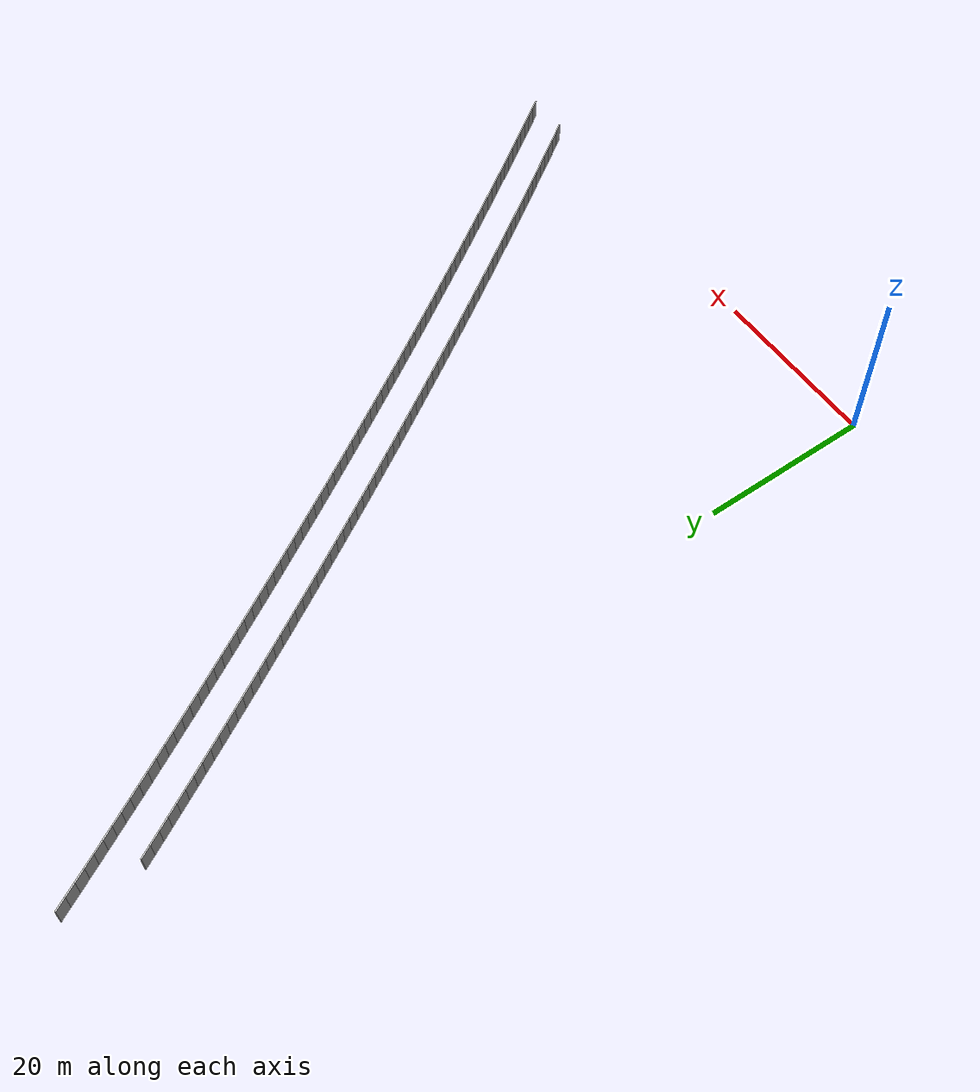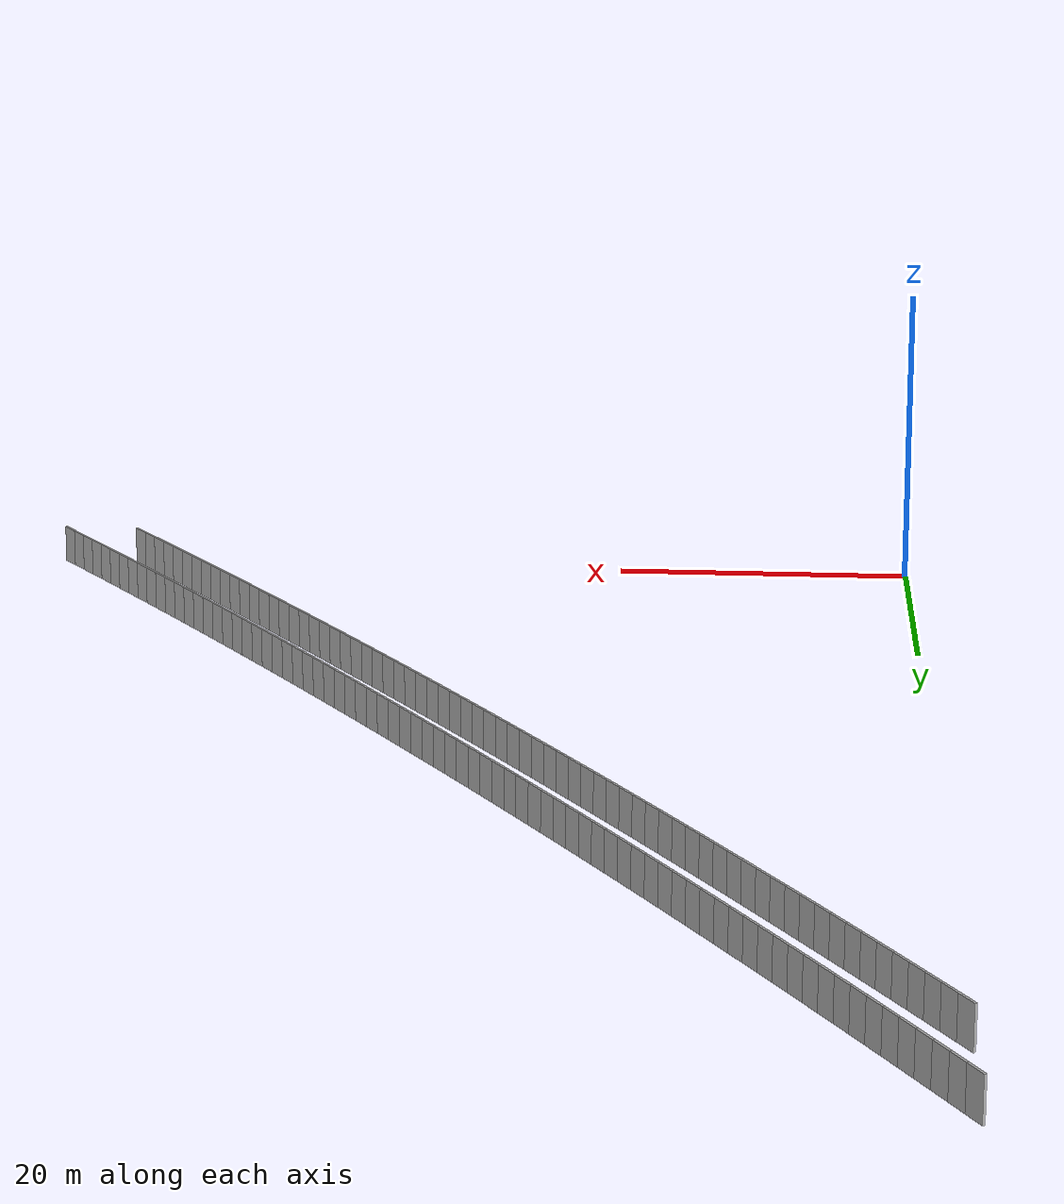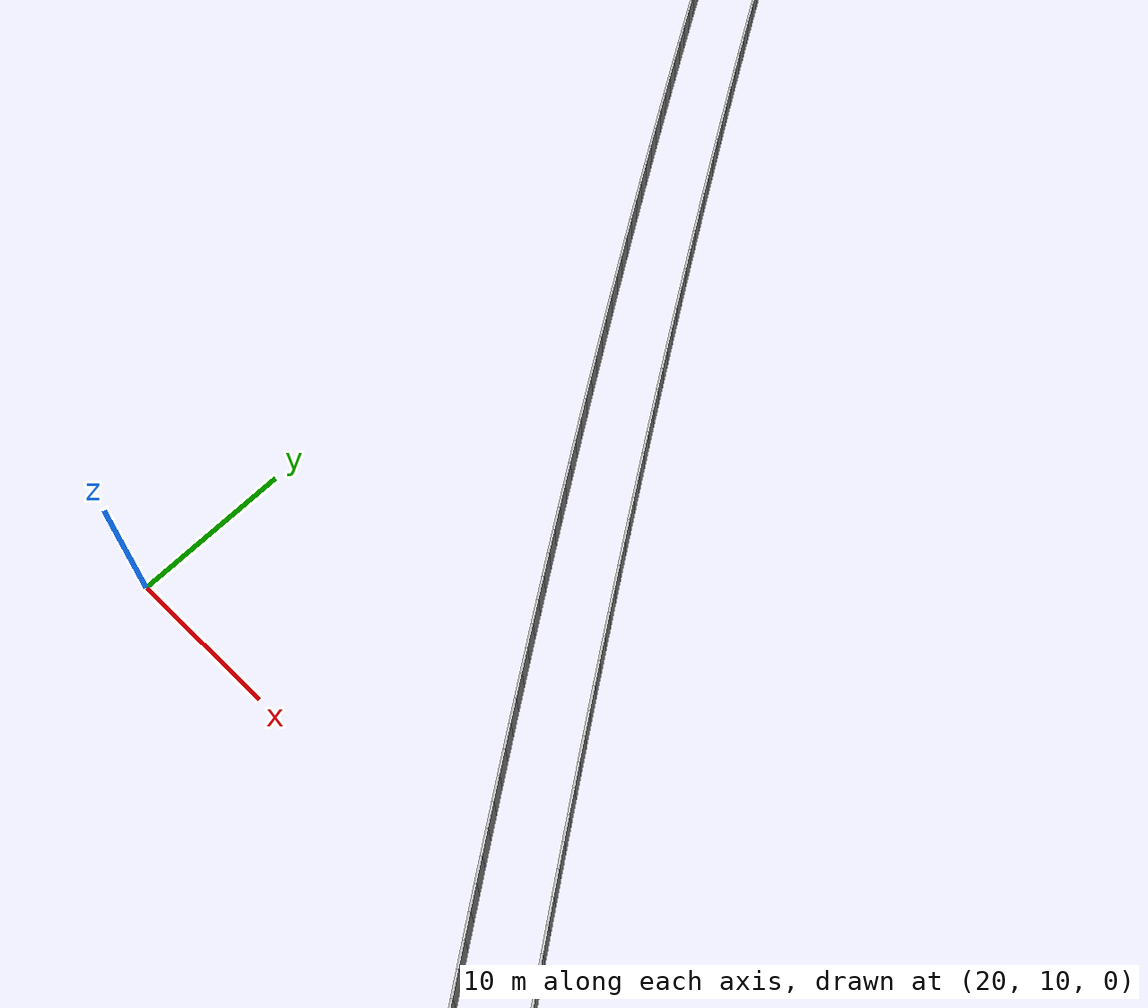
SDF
<?xml version="1.0" ?>
<sdf version="1.6">
  <model name="sps_0306">
    <pose frame="">0 0 0 0 -0 0</pose>
    <static>1</static>
    <self_collide>0</self_collide>
    <allow_auto_disable>0</allow_auto_disable>
    <link name="Wall8372">
      <kinematic>0</kinematic>
      <gravity>1</gravity>
      <self_collide>0</self_collide>
      <collision name="collision">
        <geometry>
          <box>
            <size>1.49884 0.15 2.5</size>
          </box>
        </geometry>
        <pose frame="">0 0 0 0 -0 0</pose>
      </collision>
      <visual name="visual">
        <geometry>
          <box>
            <size>1.49884 0.15 2.5</size>
          </box>
        </geometry>
        <pose frame="">0 0 0 0 -0 0</pose>
        <cast_shadows>1</cast_shadows>
        <transparency>0.0</transparency>
      </visual>
      <pose frame="">0.592246 86.9346 1.25 0 0 -1.0703</pose>
    </link>
    <link name="Wall8373">
      <kinematic>0</kinematic>
      <gravity>1</gravity>
      <self_collide>0</self_collide>
      <collision name="collision">
        <geometry>
          <box>
            <size>1.49901 0.15 2.5</size>
          </box>
        </geometry>
        <pose frame="">0 0 0 0 -0 0</pose>
      </collision>
      <visual name="visual">
        <geometry>
          <box>
            <size>1.49901 0.15 2.5</size>
          </box>
        </geometry>
        <pose frame="">0 0 0 0 -0 0</pose>
        <cast_shadows>1</cast_shadows>
        <transparency>0.0</transparency>
      </visual>
      <pose frame="">1.31255 85.6201 1.25 0 0 -1.06874</pose>
    </link>
    <link name="Wall8374">
      <kinematic>0</kinematic>
      <gravity>1</gravity>
      <self_collide>0</self_collide>
      <collision name="collision">
        <geometry>
          <box>
            <size>1.49908 0.15 2.5</size>
          </box>
        </geometry>
        <pose frame="">0 0 0 0 -0 0</pose>
      </collision>
      <visual name="visual">
        <geometry>
          <box>
            <size>1.49908 0.15 2.5</size>
          </box>
        </geometry>
        <pose frame="">0 0 0 0 -0 0</pose>
        <cast_shadows>1</cast_shadows>
        <transparency>0.0</transparency>
      </visual>
      <pose frame="">2.03493 84.3066 1.25 0 0 -1.06723</pose>
    </link>
    <link name="Wall8375">
      <kinematic>0</kinematic>
      <gravity>1</gravity>
      <self_collide>0</self_collide>
      <collision name="collision">
        <geometry>
          <box>
            <size>1.49903 0.15 2.5</size>
          </box>
        </geometry>
        <pose frame="">0 0 0 0 -0 0</pose>
      </collision>
      <visual name="visual">
        <geometry>
          <box>
            <size>1.49903 0.15 2.5</size>
          </box>
        </geometry>
        <pose frame="">0 0 0 0 -0 0</pose>
        <cast_shadows>1</cast_shadows>
        <transparency>0.0</transparency>
      </visual>
      <pose frame="">2.75933 82.9942 1.25 0 0 -1.06568</pose>
    </link>
    <link name="Wall8376">
      <kinematic>0</kinematic>
      <gravity>1</gravity>
      <self_collide>0</self_collide>
      <collision name="collision">
        <geometry>
          <box>
            <size>1.49894 0.15 2.5</size>
          </box>
        </geometry>
        <pose frame="">0 0 0 0 -0 0</pose>
      </collision>
      <visual name="visual">
        <geometry>
          <box>
            <size>1.49894 0.15 2.5</size>
          </box>
        </geometry>
        <pose frame="">0 0 0 0 -0 0</pose>
        <cast_shadows>1</cast_shadows>
        <transparency>0.0</transparency>
      </visual>
      <pose frame="">3.48574 81.683 1.25 0 0 -1.06411</pose>
    </link>
    <link name="Wall8377">
      <kinematic>0</kinematic>
      <gravity>1</gravity>
      <self_collide>0</self_collide>
      <collision name="collision">
        <geometry>
          <box>
            <size>1.49894 0.15 2.5</size>
          </box>
        </geometry>
        <pose frame="">0 0 0 0 -0 0</pose>
      </collision>
      <visual name="visual">
        <geometry>
          <box>
            <size>1.49894 0.15 2.5</size>
          </box>
        </geometry>
        <pose frame="">0 0 0 0 -0 0</pose>
        <cast_shadows>1</cast_shadows>
        <transparency>0.0</transparency>
      </visual>
      <pose frame="">4.21426 80.373 1.25 0 0 -1.06243</pose>
    </link>
    <link name="Wall8378">
      <kinematic>0</kinematic>
      <gravity>1</gravity>
      <self_collide>0</self_collide>
      <collision name="collision">
        <geometry>
          <box>
            <size>1.49883 0.15 2.5</size>
          </box>
        </geometry>
        <pose frame="">0 0 0 0 -0 0</pose>
      </collision>
      <visual name="visual">
        <geometry>
          <box>
            <size>1.49883 0.15 2.5</size>
          </box>
        </geometry>
        <pose frame="">0 0 0 0 -0 0</pose>
        <cast_shadows>1</cast_shadows>
        <transparency>0.0</transparency>
      </visual>
      <pose frame="">4.94485 79.0642 1.25 0 0 -1.06089</pose>
    </link>
    <link name="Wall8379">
      <kinematic>0</kinematic>
      <gravity>1</gravity>
      <self_collide>0</self_collide>
      <collision name="collision">
        <geometry>
          <box>
            <size>1.49901 0.15 2.5</size>
          </box>
        </geometry>
        <pose frame="">0 0 0 0 -0 0</pose>
      </collision>
      <visual name="visual">
        <geometry>
          <box>
            <size>1.49901 0.15 2.5</size>
          </box>
        </geometry>
        <pose frame="">0 0 0 0 -0 0</pose>
        <cast_shadows>1</cast_shadows>
        <transparency>0.0</transparency>
      </visual>
      <pose frame="">5.67763 77.7566 1.25 0 0 -1.05909</pose>
    </link>
    <link name="Wall8380">
      <kinematic>0</kinematic>
      <gravity>1</gravity>
      <self_collide>0</self_collide>
      <collision name="collision">
        <geometry>
          <box>
            <size>1.49906 0.15 2.5</size>
          </box>
        </geometry>
        <pose frame="">0 0 0 0 -0 0</pose>
      </collision>
      <visual name="visual">
        <geometry>
          <box>
            <size>1.49906 0.15 2.5</size>
          </box>
        </geometry>
        <pose frame="">0 0 0 0 -0 0</pose>
        <cast_shadows>1</cast_shadows>
        <transparency>0.0</transparency>
      </visual>
      <pose frame="">6.41256 76.4501 1.25 0 0 -1.05771</pose>
    </link>
    <link name="Wall8381">
      <kinematic>0</kinematic>
      <gravity>1</gravity>
      <self_collide>0</self_collide>
      <collision name="collision">
        <geometry>
          <box>
            <size>1.49905 0.15 2.5</size>
          </box>
        </geometry>
        <pose frame="">0 0 0 0 -0 0</pose>
      </collision>
      <visual name="visual">
        <geometry>
          <box>
            <size>1.49905 0.15 2.5</size>
          </box>
        </geometry>
        <pose frame="">0 0 0 0 -0 0</pose>
        <cast_shadows>1</cast_shadows>
        <transparency>0.0</transparency>
      </visual>
      <pose frame="">7.14947 75.1447 1.25 0 0 -1.05607</pose>
    </link>
    <link name="Wall8382">
      <kinematic>0</kinematic>
      <gravity>1</gravity>
      <self_collide>0</self_collide>
      <collision name="collision">
        <geometry>
          <box>
            <size>1.49867 0.15 2.5</size>
          </box>
        </geometry>
        <pose frame="">0 0 0 0 -0 0</pose>
      </collision>
      <visual name="visual">
        <geometry>
          <box>
            <size>1.49867 0.15 2.5</size>
          </box>
        </geometry>
        <pose frame="">0 0 0 0 -0 0</pose>
        <cast_shadows>1</cast_shadows>
        <transparency>0.0</transparency>
      </visual>
      <pose frame="">7.88836 73.8406 1.25 0 0 -1.05452</pose>
    </link>
    <link name="Wall8383">
      <kinematic>0</kinematic>
      <gravity>1</gravity>
      <self_collide>0</self_collide>
      <collision name="collision">
        <geometry>
          <box>
            <size>1.49896 0.15 2.5</size>
          </box>
        </geometry>
        <pose frame="">0 0 0 0 -0 0</pose>
      </collision>
      <visual name="visual">
        <geometry>
          <box>
            <size>1.49896 0.15 2.5</size>
          </box>
        </geometry>
        <pose frame="">0 0 0 0 -0 0</pose>
        <cast_shadows>1</cast_shadows>
        <transparency>0.0</transparency>
      </visual>
      <pose frame="">8.62926 72.5377 1.25 0 0 -1.05295</pose>
    </link>
    <link name="Wall8384">
      <kinematic>0</kinematic>
      <gravity>1</gravity>
      <self_collide>0</self_collide>
      <collision name="collision">
        <geometry>
          <box>
            <size>1.4989 0.15 2.5</size>
          </box>
        </geometry>
        <pose frame="">0 0 0 0 -0 0</pose>
      </collision>
      <visual name="visual">
        <geometry>
          <box>
            <size>1.4989 0.15 2.5</size>
          </box>
        </geometry>
        <pose frame="">0 0 0 0 -0 0</pose>
        <cast_shadows>1</cast_shadows>
        <transparency>0.0</transparency>
      </visual>
      <pose frame="">9.37228 71.2359 1.25 0 0 -1.05138</pose>
    </link>
    <link name="Wall8385">
      <kinematic>0</kinematic>
      <gravity>1</gravity>
      <self_collide>0</self_collide>
      <collision name="collision">
        <geometry>
          <box>
            <size>1.49906 0.15 2.5</size>
          </box>
        </geometry>
        <pose frame="">0 0 0 0 -0 0</pose>
      </collision>
      <visual name="visual">
        <geometry>
          <box>
            <size>1.49906 0.15 2.5</size>
          </box>
        </geometry>
        <pose frame="">0 0 0 0 -0 0</pose>
        <cast_shadows>1</cast_shadows>
        <transparency>0.0</transparency>
      </visual>
      <pose frame="">10.1174 69.9352 1.25 0 0 -1.0498</pose>
    </link>
    <link name="Wall8386">
      <kinematic>0</kinematic>
      <gravity>1</gravity>
      <self_collide>0</self_collide>
      <collision name="collision">
        <geometry>
          <box>
            <size>1.49881 0.15 2.5</size>
          </box>
        </geometry>
        <pose frame="">0 0 0 0 -0 0</pose>
      </collision>
      <visual name="visual">
        <geometry>
          <box>
            <size>1.49881 0.15 2.5</size>
          </box>
        </geometry>
        <pose frame="">0 0 0 0 -0 0</pose>
        <cast_shadows>1</cast_shadows>
        <transparency>0.0</transparency>
      </visual>
      <pose frame="">10.8644 68.6357 1.25 0 0 -1.04829</pose>
    </link>
    <link name="Wall8387">
      <kinematic>0</kinematic>
      <gravity>1</gravity>
      <self_collide>0</self_collide>
      <collision name="collision">
        <geometry>
          <box>
            <size>1.49904 0.15 2.5</size>
          </box>
        </geometry>
        <pose frame="">0 0 0 0 -0 0</pose>
      </collision>
      <visual name="visual">
        <geometry>
          <box>
            <size>1.49904 0.15 2.5</size>
          </box>
        </geometry>
        <pose frame="">0 0 0 0 -0 0</pose>
        <cast_shadows>1</cast_shadows>
        <transparency>0.0</transparency>
      </visual>
      <pose frame="">11.6135 67.3374 1.25 0 0 -1.04664</pose>
    </link>
    <link name="Wall8388">
      <kinematic>0</kinematic>
      <gravity>1</gravity>
      <self_collide>0</self_collide>
      <collision name="collision">
        <geometry>
          <box>
            <size>1.49881 0.15 2.5</size>
          </box>
        </geometry>
        <pose frame="">0 0 0 0 -0 0</pose>
      </collision>
      <visual name="visual">
        <geometry>
          <box>
            <size>1.49881 0.15 2.5</size>
          </box>
        </geometry>
        <pose frame="">0 0 0 0 -0 0</pose>
        <cast_shadows>1</cast_shadows>
        <transparency>0.0</transparency>
      </visual>
      <pose frame="">12.3648 66.0403 1.25 0 0 -1.04504</pose>
    </link>
    <link name="Wall8389">
      <kinematic>0</kinematic>
      <gravity>1</gravity>
      <self_collide>0</self_collide>
      <collision name="collision">
        <geometry>
          <box>
            <size>1.49907 0.15 2.5</size>
          </box>
        </geometry>
        <pose frame="">0 0 0 0 -0 0</pose>
      </collision>
      <visual name="visual">
        <geometry>
          <box>
            <size>1.49907 0.15 2.5</size>
          </box>
        </geometry>
        <pose frame="">0 0 0 0 -0 0</pose>
        <cast_shadows>1</cast_shadows>
        <transparency>0.0</transparency>
      </visual>
      <pose frame="">13.1181 64.7444 1.25 0 0 -1.04345</pose>
    </link>
    <link name="Wall8390">
      <kinematic>0</kinematic>
      <gravity>1</gravity>
      <self_collide>0</self_collide>
      <collision name="collision">
        <geometry>
          <box>
            <size>1.49903 0.15 2.5</size>
          </box>
        </geometry>
        <pose frame="">0 0 0 0 -0 0</pose>
      </collision>
      <visual name="visual">
        <geometry>
          <box>
            <size>1.49903 0.15 2.5</size>
          </box>
        </geometry>
        <pose frame="">0 0 0 0 -0 0</pose>
        <cast_shadows>1</cast_shadows>
        <transparency>0.0</transparency>
      </visual>
      <pose frame="">13.8735 63.4496 1.25 0 0 -1.04188</pose>
    </link>
    <link name="Wall8391">
      <kinematic>0</kinematic>
      <gravity>1</gravity>
      <self_collide>0</self_collide>
      <collision name="collision">
        <geometry>
          <box>
            <size>1.4988 0.15 2.5</size>
          </box>
        </geometry>
        <pose frame="">0 0 0 0 -0 0</pose>
      </collision>
      <visual name="visual">
        <geometry>
          <box>
            <size>1.4988 0.15 2.5</size>
          </box>
        </geometry>
        <pose frame="">0 0 0 0 -0 0</pose>
        <cast_shadows>1</cast_shadows>
        <transparency>0.0</transparency>
      </visual>
      <pose frame="">14.6309 62.1561 1.25 0 0 -1.04028</pose>
    </link>
    <link name="Wall8392">
      <kinematic>0</kinematic>
      <gravity>1</gravity>
      <self_collide>0</self_collide>
      <collision name="collision">
        <geometry>
          <box>
            <size>1.49901 0.15 2.5</size>
          </box>
        </geometry>
        <pose frame="">0 0 0 0 -0 0</pose>
      </collision>
      <visual name="visual">
        <geometry>
          <box>
            <size>1.49901 0.15 2.5</size>
          </box>
        </geometry>
        <pose frame="">0 0 0 0 -0 0</pose>
        <cast_shadows>1</cast_shadows>
        <transparency>0.0</transparency>
      </visual>
      <pose frame="">15.3903 60.8638 1.25 0 0 -1.03876</pose>
    </link>
    <link name="Wall8393">
      <kinematic>0</kinematic>
      <gravity>1</gravity>
      <self_collide>0</self_collide>
      <collision name="collision">
        <geometry>
          <box>
            <size>1.49905 0.15 2.5</size>
          </box>
        </geometry>
        <pose frame="">0 0 0 0 -0 0</pose>
      </collision>
      <visual name="visual">
        <geometry>
          <box>
            <size>1.49905 0.15 2.5</size>
          </box>
        </geometry>
        <pose frame="">0 0 0 0 -0 0</pose>
        <cast_shadows>1</cast_shadows>
        <transparency>0.0</transparency>
      </visual>
      <pose frame="">16.1518 59.5726 1.25 0 0 -1.03712</pose>
    </link>
    <link name="Wall8394">
      <kinematic>0</kinematic>
      <gravity>1</gravity>
      <self_collide>0</self_collide>
      <collision name="collision">
        <geometry>
          <box>
            <size>1.49861 0.15 2.5</size>
          </box>
        </geometry>
        <pose frame="">0 0 0 0 -0 0</pose>
      </collision>
      <visual name="visual">
        <geometry>
          <box>
            <size>1.49861 0.15 2.5</size>
          </box>
        </geometry>
        <pose frame="">0 0 0 0 -0 0</pose>
        <cast_shadows>1</cast_shadows>
        <transparency>0.0</transparency>
      </visual>
      <pose frame="">16.9152 58.2828 1.25 0 0 -1.03552</pose>
    </link>
    <link name="Wall8395">
      <kinematic>0</kinematic>
      <gravity>1</gravity>
      <self_collide>0</self_collide>
      <collision name="collision">
        <geometry>
          <box>
            <size>1.49896 0.15 2.5</size>
          </box>
        </geometry>
        <pose frame="">0 0 0 0 -0 0</pose>
      </collision>
      <visual name="visual">
        <geometry>
          <box>
            <size>1.49896 0.15 2.5</size>
          </box>
        </geometry>
        <pose frame="">0 0 0 0 -0 0</pose>
        <cast_shadows>1</cast_shadows>
        <transparency>0.0</transparency>
      </visual>
      <pose frame="">17.6807 56.9942 1.25 0 0 -1.0341</pose>
    </link>
    <link name="Wall8396">
      <kinematic>0</kinematic>
      <gravity>1</gravity>
      <self_collide>0</self_collide>
      <collision name="collision">
        <geometry>
          <box>
            <size>1.49888 0.15 2.5</size>
          </box>
        </geometry>
        <pose frame="">0 0 0 0 -0 0</pose>
      </collision>
      <visual name="visual">
        <geometry>
          <box>
            <size>1.49888 0.15 2.5</size>
          </box>
        </geometry>
        <pose frame="">0 0 0 0 -0 0</pose>
        <cast_shadows>1</cast_shadows>
        <transparency>0.0</transparency>
      </visual>
      <pose frame="">18.4482 55.7067 1.25 0 0 -1.03236</pose>
    </link>
    <link name="Wall8397">
      <kinematic>0</kinematic>
      <gravity>1</gravity>
      <self_collide>0</self_collide>
      <collision name="collision">
        <geometry>
          <box>
            <size>1.49904 0.15 2.5</size>
          </box>
        </geometry>
        <pose frame="">0 0 0 0 -0 0</pose>
      </collision>
      <visual name="visual">
        <geometry>
          <box>
            <size>1.49904 0.15 2.5</size>
          </box>
        </geometry>
        <pose frame="">0 0 0 0 -0 0</pose>
        <cast_shadows>1</cast_shadows>
        <transparency>0.0</transparency>
      </visual>
      <pose frame="">19.2178 54.4204 1.25 0 0 -1.03091</pose>
    </link>
    <link name="Wall8398">
      <kinematic>0</kinematic>
      <gravity>1</gravity>
      <self_collide>0</self_collide>
      <collision name="collision">
        <geometry>
          <box>
            <size>1.49882 0.15 2.5</size>
          </box>
        </geometry>
        <pose frame="">0 0 0 0 -0 0</pose>
      </collision>
      <visual name="visual">
        <geometry>
          <box>
            <size>1.49882 0.15 2.5</size>
          </box>
        </geometry>
        <pose frame="">0 0 0 0 -0 0</pose>
        <cast_shadows>1</cast_shadows>
        <transparency>0.0</transparency>
      </visual>
      <pose frame="">19.9893 53.1353 1.25 0 0 -1.02925</pose>
    </link>
    <link name="Wall8399">
      <kinematic>0</kinematic>
      <gravity>1</gravity>
      <self_collide>0</self_collide>
      <collision name="collision">
        <geometry>
          <box>
            <size>1.499 0.15 2.5</size>
          </box>
        </geometry>
        <pose frame="">0 0 0 0 -0 0</pose>
      </collision>
      <visual name="visual">
        <geometry>
          <box>
            <size>1.499 0.15 2.5</size>
          </box>
        </geometry>
        <pose frame="">0 0 0 0 -0 0</pose>
        <cast_shadows>1</cast_shadows>
        <transparency>0.0</transparency>
      </visual>
      <pose frame="">20.7631 51.8515 1.25 0 0 -1.02756</pose>
    </link>
    <link name="Wall8400">
      <kinematic>0</kinematic>
      <gravity>1</gravity>
      <self_collide>0</self_collide>
      <collision name="collision">
        <geometry>
          <box>
            <size>1.49892 0.15 2.5</size>
          </box>
        </geometry>
        <pose frame="">0 0 0 0 -0 0</pose>
      </collision>
      <visual name="visual">
        <geometry>
          <box>
            <size>1.49892 0.15 2.5</size>
          </box>
        </geometry>
        <pose frame="">0 0 0 0 -0 0</pose>
        <cast_shadows>1</cast_shadows>
        <transparency>0.0</transparency>
      </visual>
      <pose frame="">21.5388 50.5689 1.25 0 0 -1.02615</pose>
    </link>
    <link name="Wall8401">
      <kinematic>0</kinematic>
      <gravity>1</gravity>
      <self_collide>0</self_collide>
      <collision name="collision">
        <geometry>
          <box>
            <size>1.49893 0.15 2.5</size>
          </box>
        </geometry>
        <pose frame="">0 0 0 0 -0 0</pose>
      </collision>
      <visual name="visual">
        <geometry>
          <box>
            <size>1.49893 0.15 2.5</size>
          </box>
        </geometry>
        <pose frame="">0 0 0 0 -0 0</pose>
        <cast_shadows>1</cast_shadows>
        <transparency>0.0</transparency>
      </visual>
      <pose frame="">22.3165 49.2875 1.25 0 0 -1.02449</pose>
    </link>
    <link name="Wall8402">
      <kinematic>0</kinematic>
      <gravity>1</gravity>
      <self_collide>0</self_collide>
      <collision name="collision">
        <geometry>
          <box>
            <size>1.49887 0.15 2.5</size>
          </box>
        </geometry>
        <pose frame="">0 0 0 0 -0 0</pose>
      </collision>
      <visual name="visual">
        <geometry>
          <box>
            <size>1.49887 0.15 2.5</size>
          </box>
        </geometry>
        <pose frame="">0 0 0 0 -0 0</pose>
        <cast_shadows>1</cast_shadows>
        <transparency>0.0</transparency>
      </visual>
      <pose frame="">23.0962 48.0074 1.25 0 0 -1.02284</pose>
    </link>
    <link name="Wall8403">
      <kinematic>0</kinematic>
      <gravity>1</gravity>
      <self_collide>0</self_collide>
      <collision name="collision">
        <geometry>
          <box>
            <size>1.49921 0.15 2.5</size>
          </box>
        </geometry>
        <pose frame="">0 0 0 0 -0 0</pose>
      </collision>
      <visual name="visual">
        <geometry>
          <box>
            <size>1.49921 0.15 2.5</size>
          </box>
        </geometry>
        <pose frame="">0 0 0 0 -0 0</pose>
        <cast_shadows>1</cast_shadows>
        <transparency>0.0</transparency>
      </visual>
      <pose frame="">23.878 46.7284 1.25 0 0 -1.02145</pose>
    </link>
    <link name="Wall8404">
      <kinematic>0</kinematic>
      <gravity>1</gravity>
      <self_collide>0</self_collide>
      <collision name="collision">
        <geometry>
          <box>
            <size>1.49876 0.15 2.5</size>
          </box>
        </geometry>
        <pose frame="">0 0 0 0 -0 0</pose>
      </collision>
      <visual name="visual">
        <geometry>
          <box>
            <size>1.49876 0.15 2.5</size>
          </box>
        </geometry>
        <pose frame="">0 0 0 0 -0 0</pose>
        <cast_shadows>1</cast_shadows>
        <transparency>0.0</transparency>
      </visual>
      <pose frame="">24.6617 45.4506 1.25 0 0 -1.01984</pose>
    </link>
    <link name="Wall8405">
      <kinematic>0</kinematic>
      <gravity>1</gravity>
      <self_collide>0</self_collide>
      <collision name="collision">
        <geometry>
          <box>
            <size>1.49892 0.15 2.5</size>
          </box>
        </geometry>
        <pose frame="">0 0 0 0 -0 0</pose>
      </collision>
      <visual name="visual">
        <geometry>
          <box>
            <size>1.49892 0.15 2.5</size>
          </box>
        </geometry>
        <pose frame="">0 0 0 0 -0 0</pose>
        <cast_shadows>1</cast_shadows>
        <transparency>0.0</transparency>
      </visual>
      <pose frame="">25.4474 44.1742 1.25 0 0 -1.01818</pose>
    </link>
    <link name="Wall8406">
      <kinematic>0</kinematic>
      <gravity>1</gravity>
      <self_collide>0</self_collide>
      <collision name="collision">
        <geometry>
          <box>
            <size>1.49904 0.15 2.5</size>
          </box>
        </geometry>
        <pose frame="">0 0 0 0 -0 0</pose>
      </collision>
      <visual name="visual">
        <geometry>
          <box>
            <size>1.49904 0.15 2.5</size>
          </box>
        </geometry>
        <pose frame="">0 0 0 0 -0 0</pose>
        <cast_shadows>1</cast_shadows>
        <transparency>0.0</transparency>
      </visual>
      <pose frame="">26.2353 42.899 1.25 0 0 -1.01651</pose>
    </link>
    <link name="Wall8407">
      <kinematic>0</kinematic>
      <gravity>1</gravity>
      <self_collide>0</self_collide>
      <collision name="collision">
        <geometry>
          <box>
            <size>1.49897 0.15 2.5</size>
          </box>
        </geometry>
        <pose frame="">0 0 0 0 -0 0</pose>
      </collision>
      <visual name="visual">
        <geometry>
          <box>
            <size>1.49897 0.15 2.5</size>
          </box>
        </geometry>
        <pose frame="">0 0 0 0 -0 0</pose>
        <cast_shadows>1</cast_shadows>
        <transparency>0.0</transparency>
      </visual>
      <pose frame="">27.0253 41.625 1.25 0 0 -1.01504</pose>
    </link>
    <link name="Wall8408">
      <kinematic>0</kinematic>
      <gravity>1</gravity>
      <self_collide>0</self_collide>
      <collision name="collision">
        <geometry>
          <box>
            <size>1.49901 0.15 2.5</size>
          </box>
        </geometry>
        <pose frame="">0 0 0 0 -0 0</pose>
      </collision>
      <visual name="visual">
        <geometry>
          <box>
            <size>1.49901 0.15 2.5</size>
          </box>
        </geometry>
        <pose frame="">0 0 0 0 -0 0</pose>
        <cast_shadows>1</cast_shadows>
        <transparency>0.0</transparency>
      </visual>
      <pose frame="">27.8171 40.3522 1.25 0 0 -1.01353</pose>
    </link>
    <link name="Wall8409">
      <kinematic>0</kinematic>
      <gravity>1</gravity>
      <self_collide>0</self_collide>
      <collision name="collision">
        <geometry>
          <box>
            <size>1.49889 0.15 2.5</size>
          </box>
        </geometry>
        <pose frame="">0 0 0 0 -0 0</pose>
      </collision>
      <visual name="visual">
        <geometry>
          <box>
            <size>1.49889 0.15 2.5</size>
          </box>
        </geometry>
        <pose frame="">0 0 0 0 -0 0</pose>
        <cast_shadows>1</cast_shadows>
        <transparency>0.0</transparency>
      </visual>
      <pose frame="">28.6109 39.0807 1.25 0 0 -1.01189</pose>
    </link>
    <link name="Wall8410">
      <kinematic>0</kinematic>
      <gravity>1</gravity>
      <self_collide>0</self_collide>
      <collision name="collision">
        <geometry>
          <box>
            <size>1.49893 0.15 2.5</size>
          </box>
        </geometry>
        <pose frame="">0 0 0 0 -0 0</pose>
      </collision>
      <visual name="visual">
        <geometry>
          <box>
            <size>1.49893 0.15 2.5</size>
          </box>
        </geometry>
        <pose frame="">0 0 0 0 -0 0</pose>
        <cast_shadows>1</cast_shadows>
        <transparency>0.0</transparency>
      </visual>
      <pose frame="">29.4067 37.8105 1.25 0 0 -1.01032</pose>
    </link>
    <link name="Wall8411">
      <kinematic>0</kinematic>
      <gravity>1</gravity>
      <self_collide>0</self_collide>
      <collision name="collision">
        <geometry>
          <box>
            <size>1.49878 0.15 2.5</size>
          </box>
        </geometry>
        <pose frame="">0 0 0 0 -0 0</pose>
      </collision>
      <visual name="visual">
        <geometry>
          <box>
            <size>1.49878 0.15 2.5</size>
          </box>
        </geometry>
        <pose frame="">0 0 0 0 -0 0</pose>
        <cast_shadows>1</cast_shadows>
        <transparency>0.0</transparency>
      </visual>
      <pose frame="">30.2045 36.5416 1.25 0 0 -1.00872</pose>
    </link>
    <link name="Wall8412">
      <kinematic>0</kinematic>
      <gravity>1</gravity>
      <self_collide>0</self_collide>
      <collision name="collision">
        <geometry>
          <box>
            <size>1.49906 0.15 2.5</size>
          </box>
        </geometry>
        <pose frame="">0 0 0 0 -0 0</pose>
      </collision>
      <visual name="visual">
        <geometry>
          <box>
            <size>1.49906 0.15 2.5</size>
          </box>
        </geometry>
        <pose frame="">0 0 0 0 -0 0</pose>
        <cast_shadows>1</cast_shadows>
        <transparency>0.0</transparency>
      </visual>
      <pose frame="">31.0043 35.2739 1.25 0 0 -1.0072</pose>
    </link>
    <link name="Wall8413">
      <kinematic>0</kinematic>
      <gravity>1</gravity>
      <self_collide>0</self_collide>
      <collision name="collision">
        <geometry>
          <box>
            <size>1.49901 0.15 2.5</size>
          </box>
        </geometry>
        <pose frame="">0 0 0 0 -0 0</pose>
      </collision>
      <visual name="visual">
        <geometry>
          <box>
            <size>1.49901 0.15 2.5</size>
          </box>
        </geometry>
        <pose frame="">0 0 0 0 -0 0</pose>
        <cast_shadows>1</cast_shadows>
        <transparency>0.0</transparency>
      </visual>
      <pose frame="">31.8062 34.0074 1.25 0 0 -1.00549</pose>
    </link>
    <link name="Wall8414">
      <kinematic>0</kinematic>
      <gravity>1</gravity>
      <self_collide>0</self_collide>
      <collision name="collision">
        <geometry>
          <box>
            <size>1.49897 0.15 2.5</size>
          </box>
        </geometry>
        <pose frame="">0 0 0 0 -0 0</pose>
      </collision>
      <visual name="visual">
        <geometry>
          <box>
            <size>1.49897 0.15 2.5</size>
          </box>
        </geometry>
        <pose frame="">0 0 0 0 -0 0</pose>
        <cast_shadows>1</cast_shadows>
        <transparency>0.0</transparency>
      </visual>
      <pose frame="">32.6101 32.7422 1.25 0 0 -1.00403</pose>
    </link>
    <link name="Wall8415">
      <kinematic>0</kinematic>
      <gravity>1</gravity>
      <self_collide>0</self_collide>
      <collision name="collision">
        <geometry>
          <box>
            <size>1.49883 0.15 2.5</size>
          </box>
        </geometry>
        <pose frame="">0 0 0 0 -0 0</pose>
      </collision>
      <visual name="visual">
        <geometry>
          <box>
            <size>1.49883 0.15 2.5</size>
          </box>
        </geometry>
        <pose frame="">0 0 0 0 -0 0</pose>
        <cast_shadows>1</cast_shadows>
        <transparency>0.0</transparency>
      </visual>
      <pose frame="">33.4159 31.4783 1.25 0 0 -1.00242</pose>
    </link>
    <link name="Wall8416">
      <kinematic>0</kinematic>
      <gravity>1</gravity>
      <self_collide>0</self_collide>
      <collision name="collision">
        <geometry>
          <box>
            <size>1.49907 0.15 2.5</size>
          </box>
        </geometry>
        <pose frame="">0 0 0 0 -0 0</pose>
      </collision>
      <visual name="visual">
        <geometry>
          <box>
            <size>1.49907 0.15 2.5</size>
          </box>
        </geometry>
        <pose frame="">0 0 0 0 -0 0</pose>
        <cast_shadows>1</cast_shadows>
        <transparency>0.0</transparency>
      </visual>
      <pose frame="">34.2237 30.2157 1.25 0 0 -1.00074</pose>
    </link>
    <link name="Wall8417">
      <kinematic>0</kinematic>
      <gravity>1</gravity>
      <self_collide>0</self_collide>
      <collision name="collision">
        <geometry>
          <box>
            <size>1.4988 0.15 2.5</size>
          </box>
        </geometry>
        <pose frame="">0 0 0 0 -0 0</pose>
      </collision>
      <visual name="visual">
        <geometry>
          <box>
            <size>1.4988 0.15 2.5</size>
          </box>
        </geometry>
        <pose frame="">0 0 0 0 -0 0</pose>
        <cast_shadows>1</cast_shadows>
        <transparency>0.0</transparency>
      </visual>
      <pose frame="">35.0337 28.9544 1.25 0 0 -0.999217</pose>
    </link>
    <link name="Wall8418">
      <kinematic>0</kinematic>
      <gravity>1</gravity>
      <self_collide>0</self_collide>
      <collision name="collision">
        <geometry>
          <box>
            <size>1.49901 0.15 2.5</size>
          </box>
        </geometry>
        <pose frame="">0 0 0 0 -0 0</pose>
      </collision>
      <visual name="visual">
        <geometry>
          <box>
            <size>1.49901 0.15 2.5</size>
          </box>
        </geometry>
        <pose frame="">0 0 0 0 -0 0</pose>
        <cast_shadows>1</cast_shadows>
        <transparency>0.0</transparency>
      </visual>
      <pose frame="">35.8455 27.6944 1.25 0 0 -0.997565</pose>
    </link>
    <link name="Wall8419">
      <kinematic>0</kinematic>
      <gravity>1</gravity>
      <self_collide>0</self_collide>
      <collision name="collision">
        <geometry>
          <box>
            <size>1.49903 0.15 2.5</size>
          </box>
        </geometry>
        <pose frame="">0 0 0 0 -0 0</pose>
      </collision>
      <visual name="visual">
        <geometry>
          <box>
            <size>1.49903 0.15 2.5</size>
          </box>
        </geometry>
        <pose frame="">0 0 0 0 -0 0</pose>
        <cast_shadows>1</cast_shadows>
        <transparency>0.0</transparency>
      </visual>
      <pose frame="">36.6594 26.4356 1.25 0 0 -0.996119</pose>
    </link>
    <link name="Wall8420">
      <kinematic>0</kinematic>
      <gravity>1</gravity>
      <self_collide>0</self_collide>
      <collision name="collision">
        <geometry>
          <box>
            <size>1.49887 0.15 2.5</size>
          </box>
        </geometry>
        <pose frame="">0 0 0 0 -0 0</pose>
      </collision>
      <visual name="visual">
        <geometry>
          <box>
            <size>1.49887 0.15 2.5</size>
          </box>
        </geometry>
        <pose frame="">0 0 0 0 -0 0</pose>
        <cast_shadows>1</cast_shadows>
        <transparency>0.0</transparency>
      </visual>
      <pose frame="">37.4752 25.1781 1.25 0 0 -0.994495</pose>
    </link>
    <link name="Wall8421">
      <kinematic>0</kinematic>
      <gravity>1</gravity>
      <self_collide>0</self_collide>
      <collision name="collision">
        <geometry>
          <box>
            <size>1.49854 0.15 2.5</size>
          </box>
        </geometry>
        <pose frame="">0 0 0 0 -0 0</pose>
      </collision>
      <visual name="visual">
        <geometry>
          <box>
            <size>1.49854 0.15 2.5</size>
          </box>
        </geometry>
        <pose frame="">0 0 0 0 -0 0</pose>
        <cast_shadows>1</cast_shadows>
        <transparency>0.0</transparency>
      </visual>
      <pose frame="">38.2929 23.9221 1.25 0 0 -0.992893</pose>
    </link>
    <link name="Wall8422">
      <kinematic>0</kinematic>
      <gravity>1</gravity>
      <self_collide>0</self_collide>
      <collision name="collision">
        <geometry>
          <box>
            <size>1.49892 0.15 2.5</size>
          </box>
        </geometry>
        <pose frame="">0 0 0 0 -0 0</pose>
      </collision>
      <visual name="visual">
        <geometry>
          <box>
            <size>1.49892 0.15 2.5</size>
          </box>
        </geometry>
        <pose frame="">0 0 0 0 -0 0</pose>
        <cast_shadows>1</cast_shadows>
        <transparency>0.0</transparency>
      </visual>
      <pose frame="">39.1126 22.6674 1.25 0 0 -0.991309</pose>
    </link>
    <link name="Wall8423">
      <kinematic>0</kinematic>
      <gravity>1</gravity>
      <self_collide>0</self_collide>
      <collision name="collision">
        <geometry>
          <box>
            <size>1.4989 0.15 2.5</size>
          </box>
        </geometry>
        <pose frame="">0 0 0 0 -0 0</pose>
      </collision>
      <visual name="visual">
        <geometry>
          <box>
            <size>1.4989 0.15 2.5</size>
          </box>
        </geometry>
        <pose frame="">0 0 0 0 -0 0</pose>
        <cast_shadows>1</cast_shadows>
        <transparency>0.0</transparency>
      </visual>
      <pose frame="">39.9343 21.4138 1.25 0 0 -0.989841</pose>
    </link>
    <link name="Wall8424">
      <kinematic>0</kinematic>
      <gravity>1</gravity>
      <self_collide>0</self_collide>
      <collision name="collision">
        <geometry>
          <box>
            <size>1.4989 0.15 2.5</size>
          </box>
        </geometry>
        <pose frame="">0 0 0 0 -0 0</pose>
      </collision>
      <visual name="visual">
        <geometry>
          <box>
            <size>1.4989 0.15 2.5</size>
          </box>
        </geometry>
        <pose frame="">0 0 0 0 -0 0</pose>
        <cast_shadows>1</cast_shadows>
        <transparency>0.0</transparency>
      </visual>
      <pose frame="">40.758 20.1615 1.25 0 0 -0.988136</pose>
    </link>
    <link name="Wall8425">
      <kinematic>0</kinematic>
      <gravity>1</gravity>
      <self_collide>0</self_collide>
      <collision name="collision">
        <geometry>
          <box>
            <size>1.49908 0.15 2.5</size>
          </box>
        </geometry>
        <pose frame="">0 0 0 0 -0 0</pose>
      </collision>
      <visual name="visual">
        <geometry>
          <box>
            <size>1.49908 0.15 2.5</size>
          </box>
        </geometry>
        <pose frame="">0 0 0 0 -0 0</pose>
        <cast_shadows>1</cast_shadows>
        <transparency>0.0</transparency>
      </visual>
      <pose frame="">41.5839 18.9105 1.25 0 0 -0.986554</pose>
    </link>
    <link name="Wall8426">
      <kinematic>0</kinematic>
      <gravity>1</gravity>
      <self_collide>0</self_collide>
      <collision name="collision">
        <geometry>
          <box>
            <size>1.49885 0.15 2.5</size>
          </box>
        </geometry>
        <pose frame="">0 0 0 0 -0 0</pose>
      </collision>
      <visual name="visual">
        <geometry>
          <box>
            <size>1.49885 0.15 2.5</size>
          </box>
        </geometry>
        <pose frame="">0 0 0 0 -0 0</pose>
        <cast_shadows>1</cast_shadows>
        <transparency>0.0</transparency>
      </visual>
      <pose frame="">42.4116 17.6608 1.25 0 0 -0.985086</pose>
    </link>
    <link name="Wall8427">
      <kinematic>0</kinematic>
      <gravity>1</gravity>
      <self_collide>0</self_collide>
      <collision name="collision">
        <geometry>
          <box>
            <size>1.49888 0.15 2.5</size>
          </box>
        </geometry>
        <pose frame="">0 0 0 0 -0 0</pose>
      </collision>
      <visual name="visual">
        <geometry>
          <box>
            <size>1.49888 0.15 2.5</size>
          </box>
        </geometry>
        <pose frame="">0 0 0 0 -0 0</pose>
        <cast_shadows>1</cast_shadows>
        <transparency>0.0</transparency>
      </visual>
      <pose frame="">43.2412 16.4125 1.25 0 0 -0.983291</pose>
    </link>
    <link name="Wall8428">
      <kinematic>0</kinematic>
      <gravity>1</gravity>
      <self_collide>0</self_collide>
      <collision name="collision">
        <geometry>
          <box>
            <size>1.49893 0.15 2.5</size>
          </box>
        </geometry>
        <pose frame="">0 0 0 0 -0 0</pose>
      </collision>
      <visual name="visual">
        <geometry>
          <box>
            <size>1.49893 0.15 2.5</size>
          </box>
        </geometry>
        <pose frame="">0 0 0 0 -0 0</pose>
        <cast_shadows>1</cast_shadows>
        <transparency>0.0</transparency>
      </visual>
      <pose frame="">44.073 15.1655 1.25 0 0 -0.981845</pose>
    </link>
    <link name="Wall8429">
      <kinematic>0</kinematic>
      <gravity>1</gravity>
      <self_collide>0</self_collide>
      <collision name="collision">
        <geometry>
          <box>
            <size>1.49906 0.15 2.5</size>
          </box>
        </geometry>
        <pose frame="">0 0 0 0 -0 0</pose>
      </collision>
      <visual name="visual">
        <geometry>
          <box>
            <size>1.49906 0.15 2.5</size>
          </box>
        </geometry>
        <pose frame="">0 0 0 0 -0 0</pose>
        <cast_shadows>1</cast_shadows>
        <transparency>0.0</transparency>
      </visual>
      <pose frame="">44.9066 13.9197 1.25 0 0 -0.980332</pose>
    </link>
    <link name="Wall8430">
      <kinematic>0</kinematic>
      <gravity>1</gravity>
      <self_collide>0</self_collide>
      <collision name="collision">
        <geometry>
          <box>
            <size>1.49881 0.15 2.5</size>
          </box>
        </geometry>
        <pose frame="">0 0 0 0 -0 0</pose>
      </collision>
      <visual name="visual">
        <geometry>
          <box>
            <size>1.49881 0.15 2.5</size>
          </box>
        </geometry>
        <pose frame="">0 0 0 0 -0 0</pose>
        <cast_shadows>1</cast_shadows>
        <transparency>0.0</transparency>
      </visual>
      <pose frame="">45.7422 12.6753 1.25 0 0 -0.978604</pose>
    </link>
    <link name="Wall8431">
      <kinematic>0</kinematic>
      <gravity>1</gravity>
      <self_collide>0</self_collide>
      <collision name="collision">
        <geometry>
          <box>
            <size>1.49924 0.15 2.5</size>
          </box>
        </geometry>
        <pose frame="">0 0 0 0 -0 0</pose>
      </collision>
      <visual name="visual">
        <geometry>
          <box>
            <size>1.49924 0.15 2.5</size>
          </box>
        </geometry>
        <pose frame="">0 0 0 0 -0 0</pose>
        <cast_shadows>1</cast_shadows>
        <transparency>0.0</transparency>
      </visual>
      <pose frame="">46.5798 11.4321 1.25 0 0 -0.977227</pose>
    </link>
    <link name="Wall8432">
      <kinematic>0</kinematic>
      <gravity>1</gravity>
      <self_collide>0</self_collide>
      <collision name="collision">
        <geometry>
          <box>
            <size>1.49895 0.15 2.5</size>
          </box>
        </geometry>
        <pose frame="">0 0 0 0 -0 0</pose>
      </collision>
      <visual name="visual">
        <geometry>
          <box>
            <size>1.49895 0.15 2.5</size>
          </box>
        </geometry>
        <pose frame="">0 0 0 0 -0 0</pose>
        <cast_shadows>1</cast_shadows>
        <transparency>0.0</transparency>
      </visual>
      <pose frame="">47.4192 10.1901 1.25 0 0 -0.975622</pose>
    </link>
    <link name="Wall8433">
      <kinematic>0</kinematic>
      <gravity>1</gravity>
      <self_collide>0</self_collide>
      <collision name="collision">
        <geometry>
          <box>
            <size>1.49903 0.15 2.5</size>
          </box>
        </geometry>
        <pose frame="">0 0 0 0 -0 0</pose>
      </collision>
      <visual name="visual">
        <geometry>
          <box>
            <size>1.49903 0.15 2.5</size>
          </box>
        </geometry>
        <pose frame="">0 0 0 0 -0 0</pose>
        <cast_shadows>1</cast_shadows>
        <transparency>0.0</transparency>
      </visual>
      <pose frame="">48.2607 8.94957 1.25 0 0 -0.973884</pose>
    </link>
    <link name="Wall8434">
      <kinematic>0</kinematic>
      <gravity>1</gravity>
      <self_collide>0</self_collide>
      <collision name="collision">
        <geometry>
          <box>
            <size>1.49885 0.15 2.5</size>
          </box>
        </geometry>
        <pose frame="">0 0 0 0 -0 0</pose>
      </collision>
      <visual name="visual">
        <geometry>
          <box>
            <size>1.49885 0.15 2.5</size>
          </box>
        </geometry>
        <pose frame="">0 0 0 0 -0 0</pose>
        <cast_shadows>1</cast_shadows>
        <transparency>0.0</transparency>
      </visual>
      <pose frame="">49.1042 7.71049 1.25 0 0 -0.972324</pose>
    </link>
    <link name="Wall8435">
      <kinematic>0</kinematic>
      <gravity>1</gravity>
      <self_collide>0</self_collide>
      <collision name="collision">
        <geometry>
          <box>
            <size>1.49894 0.15 2.5</size>
          </box>
        </geometry>
        <pose frame="">0 0 0 0 -0 0</pose>
      </collision>
      <visual name="visual">
        <geometry>
          <box>
            <size>1.49894 0.15 2.5</size>
          </box>
        </geometry>
        <pose frame="">0 0 0 0 -0 0</pose>
        <cast_shadows>1</cast_shadows>
        <transparency>0.0</transparency>
      </visual>
      <pose frame="">49.9495 6.4727 1.25 0 0 -0.970935</pose>
    </link>
    <link name="Wall8436">
      <kinematic>0</kinematic>
      <gravity>1</gravity>
      <self_collide>0</self_collide>
      <collision name="collision">
        <geometry>
          <box>
            <size>1.49897 0.15 2.5</size>
          </box>
        </geometry>
        <pose frame="">0 0 0 0 -0 0</pose>
      </collision>
      <visual name="visual">
        <geometry>
          <box>
            <size>1.49897 0.15 2.5</size>
          </box>
        </geometry>
        <pose frame="">0 0 0 0 -0 0</pose>
        <cast_shadows>1</cast_shadows>
        <transparency>0.0</transparency>
      </visual>
      <pose frame="">50.7968 5.23619 1.25 0 0 -0.969174</pose>
    </link>
    <link name="Wall8437">
      <kinematic>0</kinematic>
      <gravity>1</gravity>
      <self_collide>0</self_collide>
      <collision name="collision">
        <geometry>
          <box>
            <size>1.49901 0.15 2.5</size>
          </box>
        </geometry>
        <pose frame="">0 0 0 0 -0 0</pose>
      </collision>
      <visual name="visual">
        <geometry>
          <box>
            <size>1.49901 0.15 2.5</size>
          </box>
        </geometry>
        <pose frame="">0 0 0 0 -0 0</pose>
        <cast_shadows>1</cast_shadows>
        <transparency>0.0</transparency>
      </visual>
      <pose frame="">51.6462 4.00108 1.25 0 0 -0.967559</pose>
    </link>
    <link name="Wall8438">
      <kinematic>0</kinematic>
      <gravity>1</gravity>
      <self_collide>0</self_collide>
      <collision name="collision">
        <geometry>
          <box>
            <size>1.49899 0.15 2.5</size>
          </box>
        </geometry>
        <pose frame="">0 0 0 0 -0 0</pose>
      </collision>
      <visual name="visual">
        <geometry>
          <box>
            <size>1.49899 0.15 2.5</size>
          </box>
        </geometry>
        <pose frame="">0 0 0 0 -0 0</pose>
        <cast_shadows>1</cast_shadows>
        <transparency>0.0</transparency>
      </visual>
      <pose frame="">52.4976 2.76729 1.25 0 0 -0.966068</pose>
    </link>
    <link name="Wall8439">
      <kinematic>0</kinematic>
      <gravity>1</gravity>
      <self_collide>0</self_collide>
      <collision name="collision">
        <geometry>
          <box>
            <size>1.49885 0.15 2.5</size>
          </box>
        </geometry>
        <pose frame="">0 0 0 0 -0 0</pose>
      </collision>
      <visual name="visual">
        <geometry>
          <box>
            <size>1.49885 0.15 2.5</size>
          </box>
        </geometry>
        <pose frame="">0 0 0 0 -0 0</pose>
        <cast_shadows>1</cast_shadows>
        <transparency>0.0</transparency>
      </visual>
      <pose frame="">53.3508 1.5349 1.25 0 0 -0.964417</pose>
    </link>
    <link name="Wall8440">
      <kinematic>0</kinematic>
      <gravity>1</gravity>
      <self_collide>0</self_collide>
      <collision name="collision">
        <geometry>
          <box>
            <size>1.49889 0.15 2.5</size>
          </box>
        </geometry>
        <pose frame="">0 0 0 0 -0 0</pose>
      </collision>
      <visual name="visual">
        <geometry>
          <box>
            <size>1.49889 0.15 2.5</size>
          </box>
        </geometry>
        <pose frame="">0 0 0 0 -0 0</pose>
        <cast_shadows>1</cast_shadows>
        <transparency>0.0</transparency>
      </visual>
      <pose frame="">54.2059 0.303878 1.25 0 0 -0.962949</pose>
    </link>
    <link name="Wall9448">
      <kinematic>0</kinematic>
      <gravity>1</gravity>
      <self_collide>0</self_collide>
      <collision name="collision">
        <geometry>
          <box>
            <size>1.49239 0.15 2.5</size>
          </box>
        </geometry>
        <pose frame="">0 0 0 0 -0 0</pose>
      </collision>
      <visual name="visual">
        <geometry>
          <box>
            <size>1.49239 0.15 2.5</size>
          </box>
        </geometry>
        <pose frame="">0 0 0 0 -0 0</pose>
        <cast_shadows>1</cast_shadows>
        <transparency>0.0</transparency>
      </visual>
      <pose frame="">0.669944 95.4822 1.25 0 0 -1.07817</pose>
    </link>
    <link name="Wall9449">
      <kinematic>0</kinematic>
      <gravity>1</gravity>
      <self_collide>0</self_collide>
      <collision name="collision">
        <geometry>
          <box>
            <size>1.49243 0.15 2.5</size>
          </box>
        </geometry>
        <pose frame="">0 0 0 0 -0 0</pose>
      </collision>
      <visual name="visual">
        <geometry>
          <box>
            <size>1.49243 0.15 2.5</size>
          </box>
        </geometry>
        <pose frame="">0 0 0 0 -0 0</pose>
        <cast_shadows>1</cast_shadows>
        <transparency>0.0</transparency>
      </visual>
      <pose frame="">1.37664 94.1677 1.25 0 0 -1.07684</pose>
    </link>
    <link name="Wall9450">
      <kinematic>0</kinematic>
      <gravity>1</gravity>
      <self_collide>0</self_collide>
      <collision name="collision">
        <geometry>
          <box>
            <size>1.49267 0.15 2.5</size>
          </box>
        </geometry>
        <pose frame="">0 0 0 0 -0 0</pose>
      </collision>
      <visual name="visual">
        <geometry>
          <box>
            <size>1.49267 0.15 2.5</size>
          </box>
        </geometry>
        <pose frame="">0 0 0 0 -0 0</pose>
        <cast_shadows>1</cast_shadows>
        <transparency>0.0</transparency>
      </visual>
      <pose frame="">2.08544 92.8542 1.25 0 0 -1.07507</pose>
    </link>
    <link name="Wall9451">
      <kinematic>0</kinematic>
      <gravity>1</gravity>
      <self_collide>0</self_collide>
      <collision name="collision">
        <geometry>
          <box>
            <size>1.49196 0.15 2.5</size>
          </box>
        </geometry>
        <pose frame="">0 0 0 0 -0 0</pose>
      </collision>
      <visual name="visual">
        <geometry>
          <box>
            <size>1.49196 0.15 2.5</size>
          </box>
        </geometry>
        <pose frame="">0 0 0 0 -0 0</pose>
        <cast_shadows>1</cast_shadows>
        <transparency>0.0</transparency>
      </visual>
      <pose frame="">2.79635 91.5421 1.25 0 0 -1.07346</pose>
    </link>
    <link name="Wall9452">
      <kinematic>0</kinematic>
      <gravity>1</gravity>
      <self_collide>0</self_collide>
      <collision name="collision">
        <geometry>
          <box>
            <size>1.49247 0.15 2.5</size>
          </box>
        </geometry>
        <pose frame="">0 0 0 0 -0 0</pose>
      </collision>
      <visual name="visual">
        <geometry>
          <box>
            <size>1.49247 0.15 2.5</size>
          </box>
        </geometry>
        <pose frame="">0 0 0 0 -0 0</pose>
        <cast_shadows>1</cast_shadows>
        <transparency>0.0</transparency>
      </visual>
      <pose frame="">3.50924 90.2312 1.25 0 0 -1.07197</pose>
    </link>
    <link name="Wall9453">
      <kinematic>0</kinematic>
      <gravity>1</gravity>
      <self_collide>0</self_collide>
      <collision name="collision">
        <geometry>
          <box>
            <size>1.49232 0.15 2.5</size>
          </box>
        </geometry>
        <pose frame="">0 0 0 0 -0 0</pose>
      </collision>
      <visual name="visual">
        <geometry>
          <box>
            <size>1.49232 0.15 2.5</size>
          </box>
        </geometry>
        <pose frame="">0 0 0 0 -0 0</pose>
        <cast_shadows>1</cast_shadows>
        <transparency>0.0</transparency>
      </visual>
      <pose frame="">4.22436 88.9213 1.25 0 0 -1.07019</pose>
    </link>
    <link name="Wall9454">
      <kinematic>0</kinematic>
      <gravity>1</gravity>
      <self_collide>0</self_collide>
      <collision name="collision">
        <geometry>
          <box>
            <size>1.49257 0.15 2.5</size>
          </box>
        </geometry>
        <pose frame="">0 0 0 0 -0 0</pose>
      </collision>
      <visual name="visual">
        <geometry>
          <box>
            <size>1.49257 0.15 2.5</size>
          </box>
        </geometry>
        <pose frame="">0 0 0 0 -0 0</pose>
        <cast_shadows>1</cast_shadows>
        <transparency>0.0</transparency>
      </visual>
      <pose frame="">4.94158 87.6125 1.25 0 0 -1.06879</pose>
    </link>
    <link name="Wall9455">
      <kinematic>0</kinematic>
      <gravity>1</gravity>
      <self_collide>0</self_collide>
      <collision name="collision">
        <geometry>
          <box>
            <size>1.49222 0.15 2.5</size>
          </box>
        </geometry>
        <pose frame="">0 0 0 0 -0 0</pose>
      </collision>
      <visual name="visual">
        <geometry>
          <box>
            <size>1.49222 0.15 2.5</size>
          </box>
        </geometry>
        <pose frame="">0 0 0 0 -0 0</pose>
        <cast_shadows>1</cast_shadows>
        <transparency>0.0</transparency>
      </visual>
      <pose frame="">5.66076 86.3048 1.25 0 0 -1.06717</pose>
    </link>
    <link name="Wall9456">
      <kinematic>0</kinematic>
      <gravity>1</gravity>
      <self_collide>0</self_collide>
      <collision name="collision">
        <geometry>
          <box>
            <size>1.49235 0.15 2.5</size>
          </box>
        </geometry>
        <pose frame="">0 0 0 0 -0 0</pose>
      </collision>
      <visual name="visual">
        <geometry>
          <box>
            <size>1.49235 0.15 2.5</size>
          </box>
        </geometry>
        <pose frame="">0 0 0 0 -0 0</pose>
        <cast_shadows>1</cast_shadows>
        <transparency>0.0</transparency>
      </visual>
      <pose frame="">6.38204 84.9984 1.25 0 0 -1.06549</pose>
    </link>
    <link name="Wall9457">
      <kinematic>0</kinematic>
      <gravity>1</gravity>
      <self_collide>0</self_collide>
      <collision name="collision">
        <geometry>
          <box>
            <size>1.49246 0.15 2.5</size>
          </box>
        </geometry>
        <pose frame="">0 0 0 0 -0 0</pose>
      </collision>
      <visual name="visual">
        <geometry>
          <box>
            <size>1.49246 0.15 2.5</size>
          </box>
        </geometry>
        <pose frame="">0 0 0 0 -0 0</pose>
        <cast_shadows>1</cast_shadows>
        <transparency>0.0</transparency>
      </visual>
      <pose frame="">7.10534 83.693 1.25 0 0 -1.06417</pose>
    </link>
    <link name="Wall9458">
      <kinematic>0</kinematic>
      <gravity>1</gravity>
      <self_collide>0</self_collide>
      <collision name="collision">
        <geometry>
          <box>
            <size>1.49242 0.15 2.5</size>
          </box>
        </geometry>
        <pose frame="">0 0 0 0 -0 0</pose>
      </collision>
      <visual name="visual">
        <geometry>
          <box>
            <size>1.49242 0.15 2.5</size>
          </box>
        </geometry>
        <pose frame="">0 0 0 0 -0 0</pose>
        <cast_shadows>1</cast_shadows>
        <transparency>0.0</transparency>
      </visual>
      <pose frame="">7.83074 82.3887 1.25 0 0 -1.06229</pose>
    </link>
    <link name="Wall9459">
      <kinematic>0</kinematic>
      <gravity>1</gravity>
      <self_collide>0</self_collide>
      <collision name="collision">
        <geometry>
          <box>
            <size>1.49243 0.15 2.5</size>
          </box>
        </geometry>
        <pose frame="">0 0 0 0 -0 0</pose>
      </collision>
      <visual name="visual">
        <geometry>
          <box>
            <size>1.49243 0.15 2.5</size>
          </box>
        </geometry>
        <pose frame="">0 0 0 0 -0 0</pose>
        <cast_shadows>1</cast_shadows>
        <transparency>0.0</transparency>
      </visual>
      <pose frame="">8.55825 81.0856 1.25 0 0 -1.06093</pose>
    </link>
    <link name="Wall9460">
      <kinematic>0</kinematic>
      <gravity>1</gravity>
      <self_collide>0</self_collide>
      <collision name="collision">
        <geometry>
          <box>
            <size>1.49244 0.15 2.5</size>
          </box>
        </geometry>
        <pose frame="">0 0 0 0 -0 0</pose>
      </collision>
      <visual name="visual">
        <geometry>
          <box>
            <size>1.49244 0.15 2.5</size>
          </box>
        </geometry>
        <pose frame="">0 0 0 0 -0 0</pose>
        <cast_shadows>1</cast_shadows>
        <transparency>0.0</transparency>
      </visual>
      <pose frame="">9.28774 79.7836 1.25 0 0 -1.05925</pose>
    </link>
    <link name="Wall9461">
      <kinematic>0</kinematic>
      <gravity>1</gravity>
      <self_collide>0</self_collide>
      <collision name="collision">
        <geometry>
          <box>
            <size>1.49228 0.15 2.5</size>
          </box>
        </geometry>
        <pose frame="">0 0 0 0 -0 0</pose>
      </collision>
      <visual name="visual">
        <geometry>
          <box>
            <size>1.49228 0.15 2.5</size>
          </box>
        </geometry>
        <pose frame="">0 0 0 0 -0 0</pose>
        <cast_shadows>1</cast_shadows>
        <transparency>0.0</transparency>
      </visual>
      <pose frame="">10.0192 78.4828 1.25 0 0 -1.05778</pose>
    </link>
    <link name="Wall9462">
      <kinematic>0</kinematic>
      <gravity>1</gravity>
      <self_collide>0</self_collide>
      <collision name="collision">
        <geometry>
          <box>
            <size>1.49251 0.15 2.5</size>
          </box>
        </geometry>
        <pose frame="">0 0 0 0 -0 0</pose>
      </collision>
      <visual name="visual">
        <geometry>
          <box>
            <size>1.49251 0.15 2.5</size>
          </box>
        </geometry>
        <pose frame="">0 0 0 0 -0 0</pose>
        <cast_shadows>1</cast_shadows>
        <transparency>0.0</transparency>
      </visual>
      <pose frame="">10.7528 77.1831 1.25 0 0 -1.05617</pose>
    </link>
    <link name="Wall9463">
      <kinematic>0</kinematic>
      <gravity>1</gravity>
      <self_collide>0</self_collide>
      <collision name="collision">
        <geometry>
          <box>
            <size>1.49239 0.15 2.5</size>
          </box>
        </geometry>
        <pose frame="">0 0 0 0 -0 0</pose>
      </collision>
      <visual name="visual">
        <geometry>
          <box>
            <size>1.49239 0.15 2.5</size>
          </box>
        </geometry>
        <pose frame="">0 0 0 0 -0 0</pose>
        <cast_shadows>1</cast_shadows>
        <transparency>0.0</transparency>
      </visual>
      <pose frame="">11.4885 75.8846 1.25 0 0 -1.05449</pose>
    </link>
    <link name="Wall9464">
      <kinematic>0</kinematic>
      <gravity>1</gravity>
      <self_collide>0</self_collide>
      <collision name="collision">
        <geometry>
          <box>
            <size>1.49246 0.15 2.5</size>
          </box>
        </geometry>
        <pose frame="">0 0 0 0 -0 0</pose>
      </collision>
      <visual name="visual">
        <geometry>
          <box>
            <size>1.49246 0.15 2.5</size>
          </box>
        </geometry>
        <pose frame="">0 0 0 0 -0 0</pose>
        <cast_shadows>1</cast_shadows>
        <transparency>0.0</transparency>
      </visual>
      <pose frame="">12.2262 74.5873 1.25 0 0 -1.05291</pose>
    </link>
    <link name="Wall9465">
      <kinematic>0</kinematic>
      <gravity>1</gravity>
      <self_collide>0</self_collide>
      <collision name="collision">
        <geometry>
          <box>
            <size>1.49257 0.15 2.5</size>
          </box>
        </geometry>
        <pose frame="">0 0 0 0 -0 0</pose>
      </collision>
      <visual name="visual">
        <geometry>
          <box>
            <size>1.49257 0.15 2.5</size>
          </box>
        </geometry>
        <pose frame="">0 0 0 0 -0 0</pose>
        <cast_shadows>1</cast_shadows>
        <transparency>0.0</transparency>
      </visual>
      <pose frame="">12.9661 73.2911 1.25 0 0 -1.05131</pose>
    </link>
    <link name="Wall9466">
      <kinematic>0</kinematic>
      <gravity>1</gravity>
      <self_collide>0</self_collide>
      <collision name="collision">
        <geometry>
          <box>
            <size>1.4922 0.15 2.5</size>
          </box>
        </geometry>
        <pose frame="">0 0 0 0 -0 0</pose>
      </collision>
      <visual name="visual">
        <geometry>
          <box>
            <size>1.4922 0.15 2.5</size>
          </box>
        </geometry>
        <pose frame="">0 0 0 0 -0 0</pose>
        <cast_shadows>1</cast_shadows>
        <transparency>0.0</transparency>
      </visual>
      <pose frame="">13.708 71.9962 1.25 0 0 -1.04975</pose>
    </link>
    <link name="Wall9467">
      <kinematic>0</kinematic>
      <gravity>1</gravity>
      <self_collide>0</self_collide>
      <collision name="collision">
        <geometry>
          <box>
            <size>1.49231 0.15 2.5</size>
          </box>
        </geometry>
        <pose frame="">0 0 0 0 -0 0</pose>
      </collision>
      <visual name="visual">
        <geometry>
          <box>
            <size>1.49231 0.15 2.5</size>
          </box>
        </geometry>
        <pose frame="">0 0 0 0 -0 0</pose>
        <cast_shadows>1</cast_shadows>
        <transparency>0.0</transparency>
      </visual>
      <pose frame="">14.4518 70.7025 1.25 0 0 -1.04824</pose>
    </link>
    <link name="Wall9468">
      <kinematic>0</kinematic>
      <gravity>1</gravity>
      <self_collide>0</self_collide>
      <collision name="collision">
        <geometry>
          <box>
            <size>1.49246 0.15 2.5</size>
          </box>
        </geometry>
        <pose frame="">0 0 0 0 -0 0</pose>
      </collision>
      <visual name="visual">
        <geometry>
          <box>
            <size>1.49246 0.15 2.5</size>
          </box>
        </geometry>
        <pose frame="">0 0 0 0 -0 0</pose>
        <cast_shadows>1</cast_shadows>
        <transparency>0.0</transparency>
      </visual>
      <pose frame="">15.1977 69.4099 1.25 0 0 -1.04659</pose>
    </link>
    <link name="Wall9469">
      <kinematic>0</kinematic>
      <gravity>1</gravity>
      <self_collide>0</self_collide>
      <collision name="collision">
        <geometry>
          <box>
            <size>1.49239 0.15 2.5</size>
          </box>
        </geometry>
        <pose frame="">0 0 0 0 -0 0</pose>
      </collision>
      <visual name="visual">
        <geometry>
          <box>
            <size>1.49239 0.15 2.5</size>
          </box>
        </geometry>
        <pose frame="">0 0 0 0 -0 0</pose>
        <cast_shadows>1</cast_shadows>
        <transparency>0.0</transparency>
      </visual>
      <pose frame="">15.9456 68.1184 1.25 0 0 -1.0452</pose>
    </link>
    <link name="Wall9470">
      <kinematic>0</kinematic>
      <gravity>1</gravity>
      <self_collide>0</self_collide>
      <collision name="collision">
        <geometry>
          <box>
            <size>1.49237 0.15 2.5</size>
          </box>
        </geometry>
        <pose frame="">0 0 0 0 -0 0</pose>
      </collision>
      <visual name="visual">
        <geometry>
          <box>
            <size>1.49237 0.15 2.5</size>
          </box>
        </geometry>
        <pose frame="">0 0 0 0 -0 0</pose>
        <cast_shadows>1</cast_shadows>
        <transparency>0.0</transparency>
      </visual>
      <pose frame="">16.6955 66.8281 1.25 0 0 -1.04344</pose>
    </link>
    <link name="Wall9471">
      <kinematic>0</kinematic>
      <gravity>1</gravity>
      <self_collide>0</self_collide>
      <collision name="collision">
        <geometry>
          <box>
            <size>1.49251 0.15 2.5</size>
          </box>
        </geometry>
        <pose frame="">0 0 0 0 -0 0</pose>
      </collision>
      <visual name="visual">
        <geometry>
          <box>
            <size>1.49251 0.15 2.5</size>
          </box>
        </geometry>
        <pose frame="">0 0 0 0 -0 0</pose>
        <cast_shadows>1</cast_shadows>
        <transparency>0.0</transparency>
      </visual>
      <pose frame="">17.4476 65.539 1.25 0 0 -1.04198</pose>
    </link>
    <link name="Wall9472">
      <kinematic>0</kinematic>
      <gravity>1</gravity>
      <self_collide>0</self_collide>
      <collision name="collision">
        <geometry>
          <box>
            <size>1.49235 0.15 2.5</size>
          </box>
        </geometry>
        <pose frame="">0 0 0 0 -0 0</pose>
      </collision>
      <visual name="visual">
        <geometry>
          <box>
            <size>1.49235 0.15 2.5</size>
          </box>
        </geometry>
        <pose frame="">0 0 0 0 -0 0</pose>
        <cast_shadows>1</cast_shadows>
        <transparency>0.0</transparency>
      </visual>
      <pose frame="">18.2017 64.2511 1.25 0 0 -1.04021</pose>
    </link>
    <link name="Wall9473">
      <kinematic>0</kinematic>
      <gravity>1</gravity>
      <self_collide>0</self_collide>
      <collision name="collision">
        <geometry>
          <box>
            <size>1.49237 0.15 2.5</size>
          </box>
        </geometry>
        <pose frame="">0 0 0 0 -0 0</pose>
      </collision>
      <visual name="visual">
        <geometry>
          <box>
            <size>1.49237 0.15 2.5</size>
          </box>
        </geometry>
        <pose frame="">0 0 0 0 -0 0</pose>
        <cast_shadows>1</cast_shadows>
        <transparency>0.0</transparency>
      </visual>
      <pose frame="">18.9578 62.9645 1.25 0 0 -1.03865</pose>
    </link>
    <link name="Wall9474">
      <kinematic>0</kinematic>
      <gravity>1</gravity>
      <self_collide>0</self_collide>
      <collision name="collision">
        <geometry>
          <box>
            <size>1.4925 0.15 2.5</size>
          </box>
        </geometry>
        <pose frame="">0 0 0 0 -0 0</pose>
      </collision>
      <visual name="visual">
        <geometry>
          <box>
            <size>1.4925 0.15 2.5</size>
          </box>
        </geometry>
        <pose frame="">0 0 0 0 -0 0</pose>
        <cast_shadows>1</cast_shadows>
        <transparency>0.0</transparency>
      </visual>
      <pose frame="">19.7161 61.679 1.25 0 0 -1.03714</pose>
    </link>
    <link name="Wall9475">
      <kinematic>0</kinematic>
      <gravity>1</gravity>
      <self_collide>0</self_collide>
      <collision name="collision">
        <geometry>
          <box>
            <size>1.49225 0.15 2.5</size>
          </box>
        </geometry>
        <pose frame="">0 0 0 0 -0 0</pose>
      </collision>
      <visual name="visual">
        <geometry>
          <box>
            <size>1.49225 0.15 2.5</size>
          </box>
        </geometry>
        <pose frame="">0 0 0 0 -0 0</pose>
        <cast_shadows>1</cast_shadows>
        <transparency>0.0</transparency>
      </visual>
      <pose frame="">20.4762 60.3947 1.25 0 0 -1.03566</pose>
    </link>
    <link name="Wall9476">
      <kinematic>0</kinematic>
      <gravity>1</gravity>
      <self_collide>0</self_collide>
      <collision name="collision">
        <geometry>
          <box>
            <size>1.49232 0.15 2.5</size>
          </box>
        </geometry>
        <pose frame="">0 0 0 0 -0 0</pose>
      </collision>
      <visual name="visual">
        <geometry>
          <box>
            <size>1.49232 0.15 2.5</size>
          </box>
        </geometry>
        <pose frame="">0 0 0 0 -0 0</pose>
        <cast_shadows>1</cast_shadows>
        <transparency>0.0</transparency>
      </visual>
      <pose frame="">21.2382 59.1117 1.25 0 0 -1.03398</pose>
    </link>
    <link name="Wall9477">
      <kinematic>0</kinematic>
      <gravity>1</gravity>
      <self_collide>0</self_collide>
      <collision name="collision">
        <geometry>
          <box>
            <size>1.49215 0.15 2.5</size>
          </box>
        </geometry>
        <pose frame="">0 0 0 0 -0 0</pose>
      </collision>
      <visual name="visual">
        <geometry>
          <box>
            <size>1.49215 0.15 2.5</size>
          </box>
        </geometry>
        <pose frame="">0 0 0 0 -0 0</pose>
        <cast_shadows>1</cast_shadows>
        <transparency>0.0</transparency>
      </visual>
      <pose frame="">22.0024 57.83 1.25 0 0 -1.03233</pose>
    </link>
    <link name="Wall9478">
      <kinematic>0</kinematic>
      <gravity>1</gravity>
      <self_collide>0</self_collide>
      <collision name="collision">
        <geometry>
          <box>
            <size>1.49245 0.15 2.5</size>
          </box>
        </geometry>
        <pose frame="">0 0 0 0 -0 0</pose>
      </collision>
      <visual name="visual">
        <geometry>
          <box>
            <size>1.49245 0.15 2.5</size>
          </box>
        </geometry>
        <pose frame="">0 0 0 0 -0 0</pose>
        <cast_shadows>1</cast_shadows>
        <transparency>0.0</transparency>
      </visual>
      <pose frame="">22.7686 56.5494 1.25 0 0 -1.03088</pose>
    </link>
    <link name="Wall9479">
      <kinematic>0</kinematic>
      <gravity>1</gravity>
      <self_collide>0</self_collide>
      <collision name="collision">
        <geometry>
          <box>
            <size>1.49254 0.15 2.5</size>
          </box>
        </geometry>
        <pose frame="">0 0 0 0 -0 0</pose>
      </collision>
      <visual name="visual">
        <geometry>
          <box>
            <size>1.49254 0.15 2.5</size>
          </box>
        </geometry>
        <pose frame="">0 0 0 0 -0 0</pose>
        <cast_shadows>1</cast_shadows>
        <transparency>0.0</transparency>
      </visual>
      <pose frame="">23.5369 55.2698 1.25 0 0 -1.02935</pose>
    </link>
    <link name="Wall9480">
      <kinematic>0</kinematic>
      <gravity>1</gravity>
      <self_collide>0</self_collide>
      <collision name="collision">
        <geometry>
          <box>
            <size>1.49255 0.15 2.5</size>
          </box>
        </geometry>
        <pose frame="">0 0 0 0 -0 0</pose>
      </collision>
      <visual name="visual">
        <geometry>
          <box>
            <size>1.49255 0.15 2.5</size>
          </box>
        </geometry>
        <pose frame="">0 0 0 0 -0 0</pose>
        <cast_shadows>1</cast_shadows>
        <transparency>0.0</transparency>
      </visual>
      <pose frame="">24.3072 53.9914 1.25 0 0 -1.02768</pose>
    </link>
    <link name="Wall9481">
      <kinematic>0</kinematic>
      <gravity>1</gravity>
      <self_collide>0</self_collide>
      <collision name="collision">
        <geometry>
          <box>
            <size>1.49247 0.15 2.5</size>
          </box>
        </geometry>
        <pose frame="">0 0 0 0 -0 0</pose>
      </collision>
      <visual name="visual">
        <geometry>
          <box>
            <size>1.49247 0.15 2.5</size>
          </box>
        </geometry>
        <pose frame="">0 0 0 0 -0 0</pose>
        <cast_shadows>1</cast_shadows>
        <transparency>0.0</transparency>
      </visual>
      <pose frame="">25.0796 52.7143 1.25 0 0 -1.02602</pose>
    </link>
    <link name="Wall9482">
      <kinematic>0</kinematic>
      <gravity>1</gravity>
      <self_collide>0</self_collide>
      <collision name="collision">
        <geometry>
          <box>
            <size>1.49239 0.15 2.5</size>
          </box>
        </geometry>
        <pose frame="">0 0 0 0 -0 0</pose>
      </collision>
      <visual name="visual">
        <geometry>
          <box>
            <size>1.49239 0.15 2.5</size>
          </box>
        </geometry>
        <pose frame="">0 0 0 0 -0 0</pose>
        <cast_shadows>1</cast_shadows>
        <transparency>0.0</transparency>
      </visual>
      <pose frame="">25.854 51.4385 1.25 0 0 -1.02446</pose>
    </link>
    <link name="Wall9483">
      <kinematic>0</kinematic>
      <gravity>1</gravity>
      <self_collide>0</self_collide>
      <collision name="collision">
        <geometry>
          <box>
            <size>1.4924 0.15 2.5</size>
          </box>
        </geometry>
        <pose frame="">0 0 0 0 -0 0</pose>
      </collision>
      <visual name="visual">
        <geometry>
          <box>
            <size>1.4924 0.15 2.5</size>
          </box>
        </geometry>
        <pose frame="">0 0 0 0 -0 0</pose>
        <cast_shadows>1</cast_shadows>
        <transparency>0.0</transparency>
      </visual>
      <pose frame="">26.6303 50.1639 1.25 0 0 -1.02303</pose>
    </link>
    <link name="Wall9484">
      <kinematic>0</kinematic>
      <gravity>1</gravity>
      <self_collide>0</self_collide>
      <collision name="collision">
        <geometry>
          <box>
            <size>1.49242 0.15 2.5</size>
          </box>
        </geometry>
        <pose frame="">0 0 0 0 -0 0</pose>
      </collision>
      <visual name="visual">
        <geometry>
          <box>
            <size>1.49242 0.15 2.5</size>
          </box>
        </geometry>
        <pose frame="">0 0 0 0 -0 0</pose>
        <cast_shadows>1</cast_shadows>
        <transparency>0.0</transparency>
      </visual>
      <pose frame="">27.4086 48.8905 1.25 0 0 -1.02136</pose>
    </link>
    <link name="Wall9485">
      <kinematic>0</kinematic>
      <gravity>1</gravity>
      <self_collide>0</self_collide>
      <collision name="collision">
        <geometry>
          <box>
            <size>1.49237 0.15 2.5</size>
          </box>
        </geometry>
        <pose frame="">0 0 0 0 -0 0</pose>
      </collision>
      <visual name="visual">
        <geometry>
          <box>
            <size>1.49237 0.15 2.5</size>
          </box>
        </geometry>
        <pose frame="">0 0 0 0 -0 0</pose>
        <cast_shadows>1</cast_shadows>
        <transparency>0.0</transparency>
      </visual>
      <pose frame="">28.189 47.6184 1.25 0 0 -1.0197</pose>
    </link>
    <link name="Wall9486">
      <kinematic>0</kinematic>
      <gravity>1</gravity>
      <self_collide>0</self_collide>
      <collision name="collision">
        <geometry>
          <box>
            <size>1.49251 0.15 2.5</size>
          </box>
        </geometry>
        <pose frame="">0 0 0 0 -0 0</pose>
      </collision>
      <visual name="visual">
        <geometry>
          <box>
            <size>1.49251 0.15 2.5</size>
          </box>
        </geometry>
        <pose frame="">0 0 0 0 -0 0</pose>
        <cast_shadows>1</cast_shadows>
        <transparency>0.0</transparency>
      </visual>
      <pose frame="">28.9714 46.3475 1.25 0 0 -1.01822</pose>
    </link>
    <link name="Wall9487">
      <kinematic>0</kinematic>
      <gravity>1</gravity>
      <self_collide>0</self_collide>
      <collision name="collision">
        <geometry>
          <box>
            <size>1.49237 0.15 2.5</size>
          </box>
        </geometry>
        <pose frame="">0 0 0 0 -0 0</pose>
      </collision>
      <visual name="visual">
        <geometry>
          <box>
            <size>1.49237 0.15 2.5</size>
          </box>
        </geometry>
        <pose frame="">0 0 0 0 -0 0</pose>
        <cast_shadows>1</cast_shadows>
        <transparency>0.0</transparency>
      </visual>
      <pose frame="">29.7558 45.0778 1.25 0 0 -1.01658</pose>
    </link>
    <link name="Wall9488">
      <kinematic>0</kinematic>
      <gravity>1</gravity>
      <self_collide>0</self_collide>
      <collision name="collision">
        <geometry>
          <box>
            <size>1.49216 0.15 2.5</size>
          </box>
        </geometry>
        <pose frame="">0 0 0 0 -0 0</pose>
      </collision>
      <visual name="visual">
        <geometry>
          <box>
            <size>1.49216 0.15 2.5</size>
          </box>
        </geometry>
        <pose frame="">0 0 0 0 -0 0</pose>
        <cast_shadows>1</cast_shadows>
        <transparency>0.0</transparency>
      </visual>
      <pose frame="">30.542 43.8095 1.25 0 0 -1.0151</pose>
    </link>
    <link name="Wall9489">
      <kinematic>0</kinematic>
      <gravity>1</gravity>
      <self_collide>0</self_collide>
      <collision name="collision">
        <geometry>
          <box>
            <size>1.49247 0.15 2.5</size>
          </box>
        </geometry>
        <pose frame="">0 0 0 0 -0 0</pose>
      </collision>
      <visual name="visual">
        <geometry>
          <box>
            <size>1.49247 0.15 2.5</size>
          </box>
        </geometry>
        <pose frame="">0 0 0 0 -0 0</pose>
        <cast_shadows>1</cast_shadows>
        <transparency>0.0</transparency>
      </visual>
      <pose frame="">31.3303 42.5424 1.25 0 0 -1.01345</pose>
    </link>
    <link name="Wall9490">
      <kinematic>0</kinematic>
      <gravity>1</gravity>
      <self_collide>0</self_collide>
      <collision name="collision">
        <geometry>
          <box>
            <size>1.49232 0.15 2.5</size>
          </box>
        </geometry>
        <pose frame="">0 0 0 0 -0 0</pose>
      </collision>
      <visual name="visual">
        <geometry>
          <box>
            <size>1.49232 0.15 2.5</size>
          </box>
        </geometry>
        <pose frame="">0 0 0 0 -0 0</pose>
        <cast_shadows>1</cast_shadows>
        <transparency>0.0</transparency>
      </visual>
      <pose frame="">32.1207 41.2765 1.25 0 0 -1.01184</pose>
    </link>
    <link name="Wall9491">
      <kinematic>0</kinematic>
      <gravity>1</gravity>
      <self_collide>0</self_collide>
      <collision name="collision">
        <geometry>
          <box>
            <size>1.49251 0.15 2.5</size>
          </box>
        </geometry>
        <pose frame="">0 0 0 0 -0 0</pose>
      </collision>
      <visual name="visual">
        <geometry>
          <box>
            <size>1.49251 0.15 2.5</size>
          </box>
        </geometry>
        <pose frame="">0 0 0 0 -0 0</pose>
        <cast_shadows>1</cast_shadows>
        <transparency>0.0</transparency>
      </visual>
      <pose frame="">32.9131 40.0118 1.25 0 0 -1.01032</pose>
    </link>
    <link name="Wall9492">
      <kinematic>0</kinematic>
      <gravity>1</gravity>
      <self_collide>0</self_collide>
      <collision name="collision">
        <geometry>
          <box>
            <size>1.49235 0.15 2.5</size>
          </box>
        </geometry>
        <pose frame="">0 0 0 0 -0 0</pose>
      </collision>
      <visual name="visual">
        <geometry>
          <box>
            <size>1.49235 0.15 2.5</size>
          </box>
        </geometry>
        <pose frame="">0 0 0 0 -0 0</pose>
        <cast_shadows>1</cast_shadows>
        <transparency>0.0</transparency>
      </visual>
      <pose frame="">33.7075 38.7483 1.25 0 0 -1.00881</pose>
    </link>
    <link name="Wall9493">
      <kinematic>0</kinematic>
      <gravity>1</gravity>
      <self_collide>0</self_collide>
      <collision name="collision">
        <geometry>
          <box>
            <size>1.49245 0.15 2.5</size>
          </box>
        </geometry>
        <pose frame="">0 0 0 0 -0 0</pose>
      </collision>
      <visual name="visual">
        <geometry>
          <box>
            <size>1.49245 0.15 2.5</size>
          </box>
        </geometry>
        <pose frame="">0 0 0 0 -0 0</pose>
        <cast_shadows>1</cast_shadows>
        <transparency>0.0</transparency>
      </visual>
      <pose frame="">34.5037 37.4861 1.25 0 0 -1.00716</pose>
    </link>
    <link name="Wall9494">
      <kinematic>0</kinematic>
      <gravity>1</gravity>
      <self_collide>0</self_collide>
      <collision name="collision">
        <geometry>
          <box>
            <size>1.49238 0.15 2.5</size>
          </box>
        </geometry>
        <pose frame="">0 0 0 0 -0 0</pose>
      </collision>
      <visual name="visual">
        <geometry>
          <box>
            <size>1.49238 0.15 2.5</size>
          </box>
        </geometry>
        <pose frame="">0 0 0 0 -0 0</pose>
        <cast_shadows>1</cast_shadows>
        <transparency>0.0</transparency>
      </visual>
      <pose frame="">35.3021 36.2252 1.25 0 0 -1.00548</pose>
    </link>
    <link name="Wall9495">
      <kinematic>0</kinematic>
      <gravity>1</gravity>
      <self_collide>0</self_collide>
      <collision name="collision">
        <geometry>
          <box>
            <size>1.49245 0.15 2.5</size>
          </box>
        </geometry>
        <pose frame="">0 0 0 0 -0 0</pose>
      </collision>
      <visual name="visual">
        <geometry>
          <box>
            <size>1.49245 0.15 2.5</size>
          </box>
        </geometry>
        <pose frame="">0 0 0 0 -0 0</pose>
        <cast_shadows>1</cast_shadows>
        <transparency>0.0</transparency>
      </visual>
      <pose frame="">36.1026 34.9656 1.25 0 0 -1.00396</pose>
    </link>
    <link name="Wall9496">
      <kinematic>0</kinematic>
      <gravity>1</gravity>
      <self_collide>0</self_collide>
      <collision name="collision">
        <geometry>
          <box>
            <size>1.49245 0.15 2.5</size>
          </box>
        </geometry>
        <pose frame="">0 0 0 0 -0 0</pose>
      </collision>
      <visual name="visual">
        <geometry>
          <box>
            <size>1.49245 0.15 2.5</size>
          </box>
        </geometry>
        <pose frame="">0 0 0 0 -0 0</pose>
        <cast_shadows>1</cast_shadows>
        <transparency>0.0</transparency>
      </visual>
      <pose frame="">36.905 33.7072 1.25 0 0 -1.00236</pose>
    </link>
    <link name="Wall9497">
      <kinematic>0</kinematic>
      <gravity>1</gravity>
      <self_collide>0</self_collide>
      <collision name="collision">
        <geometry>
          <box>
            <size>1.49248 0.15 2.5</size>
          </box>
        </geometry>
        <pose frame="">0 0 0 0 -0 0</pose>
      </collision>
      <visual name="visual">
        <geometry>
          <box>
            <size>1.49248 0.15 2.5</size>
          </box>
        </geometry>
        <pose frame="">0 0 0 0 -0 0</pose>
        <cast_shadows>1</cast_shadows>
        <transparency>0.0</transparency>
      </visual>
      <pose frame="">37.7093 32.45 1.25 0 0 -1.00097</pose>
    </link>
    <link name="Wall9498">
      <kinematic>0</kinematic>
      <gravity>1</gravity>
      <self_collide>0</self_collide>
      <collision name="collision">
        <geometry>
          <box>
            <size>1.49246 0.15 2.5</size>
          </box>
        </geometry>
        <pose frame="">0 0 0 0 -0 0</pose>
      </collision>
      <visual name="visual">
        <geometry>
          <box>
            <size>1.49246 0.15 2.5</size>
          </box>
        </geometry>
        <pose frame="">0 0 0 0 -0 0</pose>
        <cast_shadows>1</cast_shadows>
        <transparency>0.0</transparency>
      </visual>
      <pose frame="">38.5156 31.1941 1.25 0 0 -0.999162</pose>
    </link>
    <link name="Wall9499">
      <kinematic>0</kinematic>
      <gravity>1</gravity>
      <self_collide>0</self_collide>
      <collision name="collision">
        <geometry>
          <box>
            <size>1.49234 0.15 2.5</size>
          </box>
        </geometry>
        <pose frame="">0 0 0 0 -0 0</pose>
      </collision>
      <visual name="visual">
        <geometry>
          <box>
            <size>1.49234 0.15 2.5</size>
          </box>
        </geometry>
        <pose frame="">0 0 0 0 -0 0</pose>
        <cast_shadows>1</cast_shadows>
        <transparency>0.0</transparency>
      </visual>
      <pose frame="">39.324 29.9396 1.25 0 0 -0.997552</pose>
    </link>
    <link name="Wall9500">
      <kinematic>0</kinematic>
      <gravity>1</gravity>
      <self_collide>0</self_collide>
      <collision name="collision">
        <geometry>
          <box>
            <size>1.49236 0.15 2.5</size>
          </box>
        </geometry>
        <pose frame="">0 0 0 0 -0 0</pose>
      </collision>
      <visual name="visual">
        <geometry>
          <box>
            <size>1.49236 0.15 2.5</size>
          </box>
        </geometry>
        <pose frame="">0 0 0 0 -0 0</pose>
        <cast_shadows>1</cast_shadows>
        <transparency>0.0</transparency>
      </visual>
      <pose frame="">40.1343 28.6864 1.25 0 0 -0.9961</pose>
    </link>
    <link name="Wall9501">
      <kinematic>0</kinematic>
      <gravity>1</gravity>
      <self_collide>0</self_collide>
      <collision name="collision">
        <geometry>
          <box>
            <size>1.4925 0.15 2.5</size>
          </box>
        </geometry>
        <pose frame="">0 0 0 0 -0 0</pose>
      </collision>
      <visual name="visual">
        <geometry>
          <box>
            <size>1.4925 0.15 2.5</size>
          </box>
        </geometry>
        <pose frame="">0 0 0 0 -0 0</pose>
        <cast_shadows>1</cast_shadows>
        <transparency>0.0</transparency>
      </visual>
      <pose frame="">40.9466 27.4344 1.25 0 0 -0.994454</pose>
    </link>
    <link name="Wall9502">
      <kinematic>0</kinematic>
      <gravity>1</gravity>
      <self_collide>0</self_collide>
      <collision name="collision">
        <geometry>
          <box>
            <size>1.49236 0.15 2.5</size>
          </box>
        </geometry>
        <pose frame="">0 0 0 0 -0 0</pose>
      </collision>
      <visual name="visual">
        <geometry>
          <box>
            <size>1.49236 0.15 2.5</size>
          </box>
        </geometry>
        <pose frame="">0 0 0 0 -0 0</pose>
        <cast_shadows>1</cast_shadows>
        <transparency>0.0</transparency>
      </visual>
      <pose frame="">41.7609 26.1837 1.25 0 0 -0.992878</pose>
    </link>
    <link name="Wall9503">
      <kinematic>0</kinematic>
      <gravity>1</gravity>
      <self_collide>0</self_collide>
      <collision name="collision">
        <geometry>
          <box>
            <size>1.49176 0.15 2.5</size>
          </box>
        </geometry>
        <pose frame="">0 0 0 0 -0 0</pose>
      </collision>
      <visual name="visual">
        <geometry>
          <box>
            <size>1.49176 0.15 2.5</size>
          </box>
        </geometry>
        <pose frame="">0 0 0 0 -0 0</pose>
        <cast_shadows>1</cast_shadows>
        <transparency>0.0</transparency>
      </visual>
      <pose frame="">42.577 24.9346 1.25 0 0 -0.991248</pose>
    </link>
    <link name="Wall9504">
      <kinematic>0</kinematic>
      <gravity>1</gravity>
      <self_collide>0</self_collide>
      <collision name="collision">
        <geometry>
          <box>
            <size>1.49254 0.15 2.5</size>
          </box>
        </geometry>
        <pose frame="">0 0 0 0 -0 0</pose>
      </collision>
      <visual name="visual">
        <geometry>
          <box>
            <size>1.49254 0.15 2.5</size>
          </box>
        </geometry>
        <pose frame="">0 0 0 0 -0 0</pose>
        <cast_shadows>1</cast_shadows>
        <transparency>0.0</transparency>
      </visual>
      <pose frame="">43.395 23.6867 1.25 0 0 -0.98978</pose>
    </link>
    <link name="Wall9505">
      <kinematic>0</kinematic>
      <gravity>1</gravity>
      <self_collide>0</self_collide>
      <collision name="collision">
        <geometry>
          <box>
            <size>1.49234 0.15 2.5</size>
          </box>
        </geometry>
        <pose frame="">0 0 0 0 -0 0</pose>
      </collision>
      <visual name="visual">
        <geometry>
          <box>
            <size>1.49234 0.15 2.5</size>
          </box>
        </geometry>
        <pose frame="">0 0 0 0 -0 0</pose>
        <cast_shadows>1</cast_shadows>
        <transparency>0.0</transparency>
      </visual>
      <pose frame="">44.2151 22.4398 1.25 0 0 -0.988273</pose>
    </link>
    <link name="Wall9506">
      <kinematic>0</kinematic>
      <gravity>1</gravity>
      <self_collide>0</self_collide>
      <collision name="collision">
        <geometry>
          <box>
            <size>1.49256 0.15 2.5</size>
          </box>
        </geometry>
        <pose frame="">0 0 0 0 -0 0</pose>
      </collision>
      <visual name="visual">
        <geometry>
          <box>
            <size>1.49256 0.15 2.5</size>
          </box>
        </geometry>
        <pose frame="">0 0 0 0 -0 0</pose>
        <cast_shadows>1</cast_shadows>
        <transparency>0.0</transparency>
      </visual>
      <pose frame="">45.0373 21.1942 1.25 0 0 -0.986559</pose>
    </link>
    <link name="Wall9507">
      <kinematic>0</kinematic>
      <gravity>1</gravity>
      <self_collide>0</self_collide>
      <collision name="collision">
        <geometry>
          <box>
            <size>1.49234 0.15 2.5</size>
          </box>
        </geometry>
        <pose frame="">0 0 0 0 -0 0</pose>
      </collision>
      <visual name="visual">
        <geometry>
          <box>
            <size>1.49234 0.15 2.5</size>
          </box>
        </geometry>
        <pose frame="">0 0 0 0 -0 0</pose>
        <cast_shadows>1</cast_shadows>
        <transparency>0.0</transparency>
      </visual>
      <pose frame="">45.8614 19.9499 1.25 0 0 -0.985085</pose>
    </link>
    <link name="Wall9508">
      <kinematic>0</kinematic>
      <gravity>1</gravity>
      <self_collide>0</self_collide>
      <collision name="collision">
        <geometry>
          <box>
            <size>1.49257 0.15 2.5</size>
          </box>
        </geometry>
        <pose frame="">0 0 0 0 -0 0</pose>
      </collision>
      <visual name="visual">
        <geometry>
          <box>
            <size>1.49257 0.15 2.5</size>
          </box>
        </geometry>
        <pose frame="">0 0 0 0 -0 0</pose>
        <cast_shadows>1</cast_shadows>
        <transparency>0.0</transparency>
      </visual>
      <pose frame="">46.6874 18.7069 1.25 0 0 -0.983372</pose>
    </link>
    <link name="Wall9509">
      <kinematic>0</kinematic>
      <gravity>1</gravity>
      <self_collide>0</self_collide>
      <collision name="collision">
        <geometry>
          <box>
            <size>1.49247 0.15 2.5</size>
          </box>
        </geometry>
        <pose frame="">0 0 0 0 -0 0</pose>
      </collision>
      <visual name="visual">
        <geometry>
          <box>
            <size>1.49247 0.15 2.5</size>
          </box>
        </geometry>
        <pose frame="">0 0 0 0 -0 0</pose>
        <cast_shadows>1</cast_shadows>
        <transparency>0.0</transparency>
      </visual>
      <pose frame="">47.5156 17.4652 1.25 0 0 -0.981852</pose>
    </link>
    <link name="Wall9510">
      <kinematic>0</kinematic>
      <gravity>1</gravity>
      <self_collide>0</self_collide>
      <collision name="collision">
        <geometry>
          <box>
            <size>1.4922 0.15 2.5</size>
          </box>
        </geometry>
        <pose frame="">0 0 0 0 -0 0</pose>
      </collision>
      <visual name="visual">
        <geometry>
          <box>
            <size>1.4922 0.15 2.5</size>
          </box>
        </geometry>
        <pose frame="">0 0 0 0 -0 0</pose>
        <cast_shadows>1</cast_shadows>
        <transparency>0.0</transparency>
      </visual>
      <pose frame="">48.3455 16.2249 1.25 0 0 -0.980355</pose>
    </link>
    <link name="Wall9511">
      <kinematic>0</kinematic>
      <gravity>1</gravity>
      <self_collide>0</self_collide>
      <collision name="collision">
        <geometry>
          <box>
            <size>1.4925 0.15 2.5</size>
          </box>
        </geometry>
        <pose frame="">0 0 0 0 -0 0</pose>
      </collision>
      <visual name="visual">
        <geometry>
          <box>
            <size>1.4925 0.15 2.5</size>
          </box>
        </geometry>
        <pose frame="">0 0 0 0 -0 0</pose>
        <cast_shadows>1</cast_shadows>
        <transparency>0.0</transparency>
      </visual>
      <pose frame="">49.1773 14.9859 1.25 0 0 -0.978665</pose>
    </link>
    <link name="Wall9512">
      <kinematic>0</kinematic>
      <gravity>1</gravity>
      <self_collide>0</self_collide>
      <collision name="collision">
        <geometry>
          <box>
            <size>1.49236 0.15 2.5</size>
          </box>
        </geometry>
        <pose frame="">0 0 0 0 -0 0</pose>
      </collision>
      <visual name="visual">
        <geometry>
          <box>
            <size>1.49236 0.15 2.5</size>
          </box>
        </geometry>
        <pose frame="">0 0 0 0 -0 0</pose>
        <cast_shadows>1</cast_shadows>
        <transparency>0.0</transparency>
      </visual>
      <pose frame="">50.0113 13.7482 1.25 0 0 -0.977122</pose>
    </link>
    <link name="Wall9513">
      <kinematic>0</kinematic>
      <gravity>1</gravity>
      <self_collide>0</self_collide>
      <collision name="collision">
        <geometry>
          <box>
            <size>1.49249 0.15 2.5</size>
          </box>
        </geometry>
        <pose frame="">0 0 0 0 -0 0</pose>
      </collision>
      <visual name="visual">
        <geometry>
          <box>
            <size>1.49249 0.15 2.5</size>
          </box>
        </geometry>
        <pose frame="">0 0 0 0 -0 0</pose>
        <cast_shadows>1</cast_shadows>
        <transparency>0.0</transparency>
      </visual>
      <pose frame="">50.8471 12.5118 1.25 0 0 -0.975603</pose>
    </link>
    <link name="Wall9514">
      <kinematic>0</kinematic>
      <gravity>1</gravity>
      <self_collide>0</self_collide>
      <collision name="collision">
        <geometry>
          <box>
            <size>1.49241 0.15 2.5</size>
          </box>
        </geometry>
        <pose frame="">0 0 0 0 -0 0</pose>
      </collision>
      <visual name="visual">
        <geometry>
          <box>
            <size>1.49241 0.15 2.5</size>
          </box>
        </geometry>
        <pose frame="">0 0 0 0 -0 0</pose>
        <cast_shadows>1</cast_shadows>
        <transparency>0.0</transparency>
      </visual>
      <pose frame="">51.6849 11.2767 1.25 0 0 -0.973935</pose>
    </link>
    <link name="Wall9515">
      <kinematic>0</kinematic>
      <gravity>1</gravity>
      <self_collide>0</self_collide>
      <collision name="collision">
        <geometry>
          <box>
            <size>1.4924 0.15 2.5</size>
          </box>
        </geometry>
        <pose frame="">0 0 0 0 -0 0</pose>
      </collision>
      <visual name="visual">
        <geometry>
          <box>
            <size>1.4924 0.15 2.5</size>
          </box>
        </geometry>
        <pose frame="">0 0 0 0 -0 0</pose>
        <cast_shadows>1</cast_shadows>
        <transparency>0.0</transparency>
      </visual>
      <pose frame="">52.5246 10.043 1.25 0 0 -0.972347</pose>
    </link>
    <link name="Wall9516">
      <kinematic>0</kinematic>
      <gravity>1</gravity>
      <self_collide>0</self_collide>
      <collision name="collision">
        <geometry>
          <box>
            <size>1.49251 0.15 2.5</size>
          </box>
        </geometry>
        <pose frame="">0 0 0 0 -0 0</pose>
      </collision>
      <visual name="visual">
        <geometry>
          <box>
            <size>1.49251 0.15 2.5</size>
          </box>
        </geometry>
        <pose frame="">0 0 0 0 -0 0</pose>
        <cast_shadows>1</cast_shadows>
        <transparency>0.0</transparency>
      </visual>
      <pose frame="">53.3664 8.81059 1.25 0 0 -0.970714</pose>
    </link>
    <link name="Wall9517">
      <kinematic>0</kinematic>
      <gravity>1</gravity>
      <self_collide>0</self_collide>
      <collision name="collision">
        <geometry>
          <box>
            <size>1.4924 0.15 2.5</size>
          </box>
        </geometry>
        <pose frame="">0 0 0 0 -0 0</pose>
      </collision>
      <visual name="visual">
        <geometry>
          <box>
            <size>1.4924 0.15 2.5</size>
          </box>
        </geometry>
        <pose frame="">0 0 0 0 -0 0</pose>
        <cast_shadows>1</cast_shadows>
        <transparency>0.0</transparency>
      </visual>
      <pose frame="">54.2102 7.57951 1.25 0 0 -0.969227</pose>
    </link>
    <link name="Wall9518">
      <kinematic>0</kinematic>
      <gravity>1</gravity>
      <self_collide>0</self_collide>
      <collision name="collision">
        <geometry>
          <box>
            <size>1.49225 0.15 2.5</size>
          </box>
        </geometry>
        <pose frame="">0 0 0 0 -0 0</pose>
      </collision>
      <visual name="visual">
        <geometry>
          <box>
            <size>1.49225 0.15 2.5</size>
          </box>
        </geometry>
        <pose frame="">0 0 0 0 -0 0</pose>
        <cast_shadows>1</cast_shadows>
        <transparency>0.0</transparency>
      </visual>
      <pose frame="">55.0557 6.34981 1.25 0 0 -0.967717</pose>
    </link>
    <link name="Wall9519">
      <kinematic>0</kinematic>
      <gravity>1</gravity>
      <self_collide>0</self_collide>
      <collision name="collision">
        <geometry>
          <box>
            <size>1.49237 0.15 2.5</size>
          </box>
        </geometry>
        <pose frame="">0 0 0 0 -0 0</pose>
      </collision>
      <visual name="visual">
        <geometry>
          <box>
            <size>1.49237 0.15 2.5</size>
          </box>
        </geometry>
        <pose frame="">0 0 0 0 -0 0</pose>
        <cast_shadows>1</cast_shadows>
        <transparency>0.0</transparency>
      </visual>
      <pose frame="">55.9032 5.1215 1.25 0 0 -0.965937</pose>
    </link>
    <link name="Wall9520">
      <kinematic>0</kinematic>
      <gravity>1</gravity>
      <self_collide>0</self_collide>
      <collision name="collision">
        <geometry>
          <box>
            <size>1.49243 0.15 2.5</size>
          </box>
        </geometry>
        <pose frame="">0 0 0 0 -0 0</pose>
      </collision>
      <visual name="visual">
        <geometry>
          <box>
            <size>1.49243 0.15 2.5</size>
          </box>
        </geometry>
        <pose frame="">0 0 0 0 -0 0</pose>
        <cast_shadows>1</cast_shadows>
        <transparency>0.0</transparency>
      </visual>
      <pose frame="">56.7527 3.89448 1.25 0 0 -0.96452</pose>
    </link>
    <link name="Wall9521">
      <kinematic>0</kinematic>
      <gravity>1</gravity>
      <self_collide>0</self_collide>
      <collision name="collision">
        <geometry>
          <box>
            <size>1.49234 0.15 2.5</size>
          </box>
        </geometry>
        <pose frame="">0 0 0 0 -0 0</pose>
      </collision>
      <visual name="visual">
        <geometry>
          <box>
            <size>1.49234 0.15 2.5</size>
          </box>
        </geometry>
        <pose frame="">0 0 0 0 -0 0</pose>
        <cast_shadows>1</cast_shadows>
        <transparency>0.0</transparency>
      </visual>
      <pose frame="">57.6041 2.66878 1.25 0 0 -0.962885</pose>
    </link>
    <link name="Wall9522">
      <kinematic>0</kinematic>
      <gravity>1</gravity>
      <self_collide>0</self_collide>
      <collision name="collision">
        <geometry>
          <box>
            <size>1.49247 0.15 2.5</size>
          </box>
        </geometry>
        <pose frame="">0 0 0 0 -0 0</pose>
      </collision>
      <visual name="visual">
        <geometry>
          <box>
            <size>1.49247 0.15 2.5</size>
          </box>
        </geometry>
        <pose frame="">0 0 0 0 -0 0</pose>
        <cast_shadows>1</cast_shadows>
        <transparency>0.0</transparency>
      </visual>
      <pose frame="">58.4574 1.44438 1.25 0 0 -0.9614</pose>
    </link>
    <link name="Wall9523">
      <kinematic>0</kinematic>
      <gravity>1</gravity>
      <self_collide>0</self_collide>
      <collision name="collision">
        <geometry>
          <box>
            <size>1.49224 0.15 2.5</size>
          </box>
        </geometry>
        <pose frame="">0 0 0 0 -0 0</pose>
      </collision>
      <visual name="visual">
        <geometry>
          <box>
            <size>1.49224 0.15 2.5</size>
          </box>
        </geometry>
        <pose frame="">0 0 0 0 -0 0</pose>
        <cast_shadows>1</cast_shadows>
        <transparency>0.0</transparency>
      </visual>
      <pose frame="">59.3126 0.221389 1.25 0 0 -0.959695</pose>
    </link>
  </model>
</sdf>
